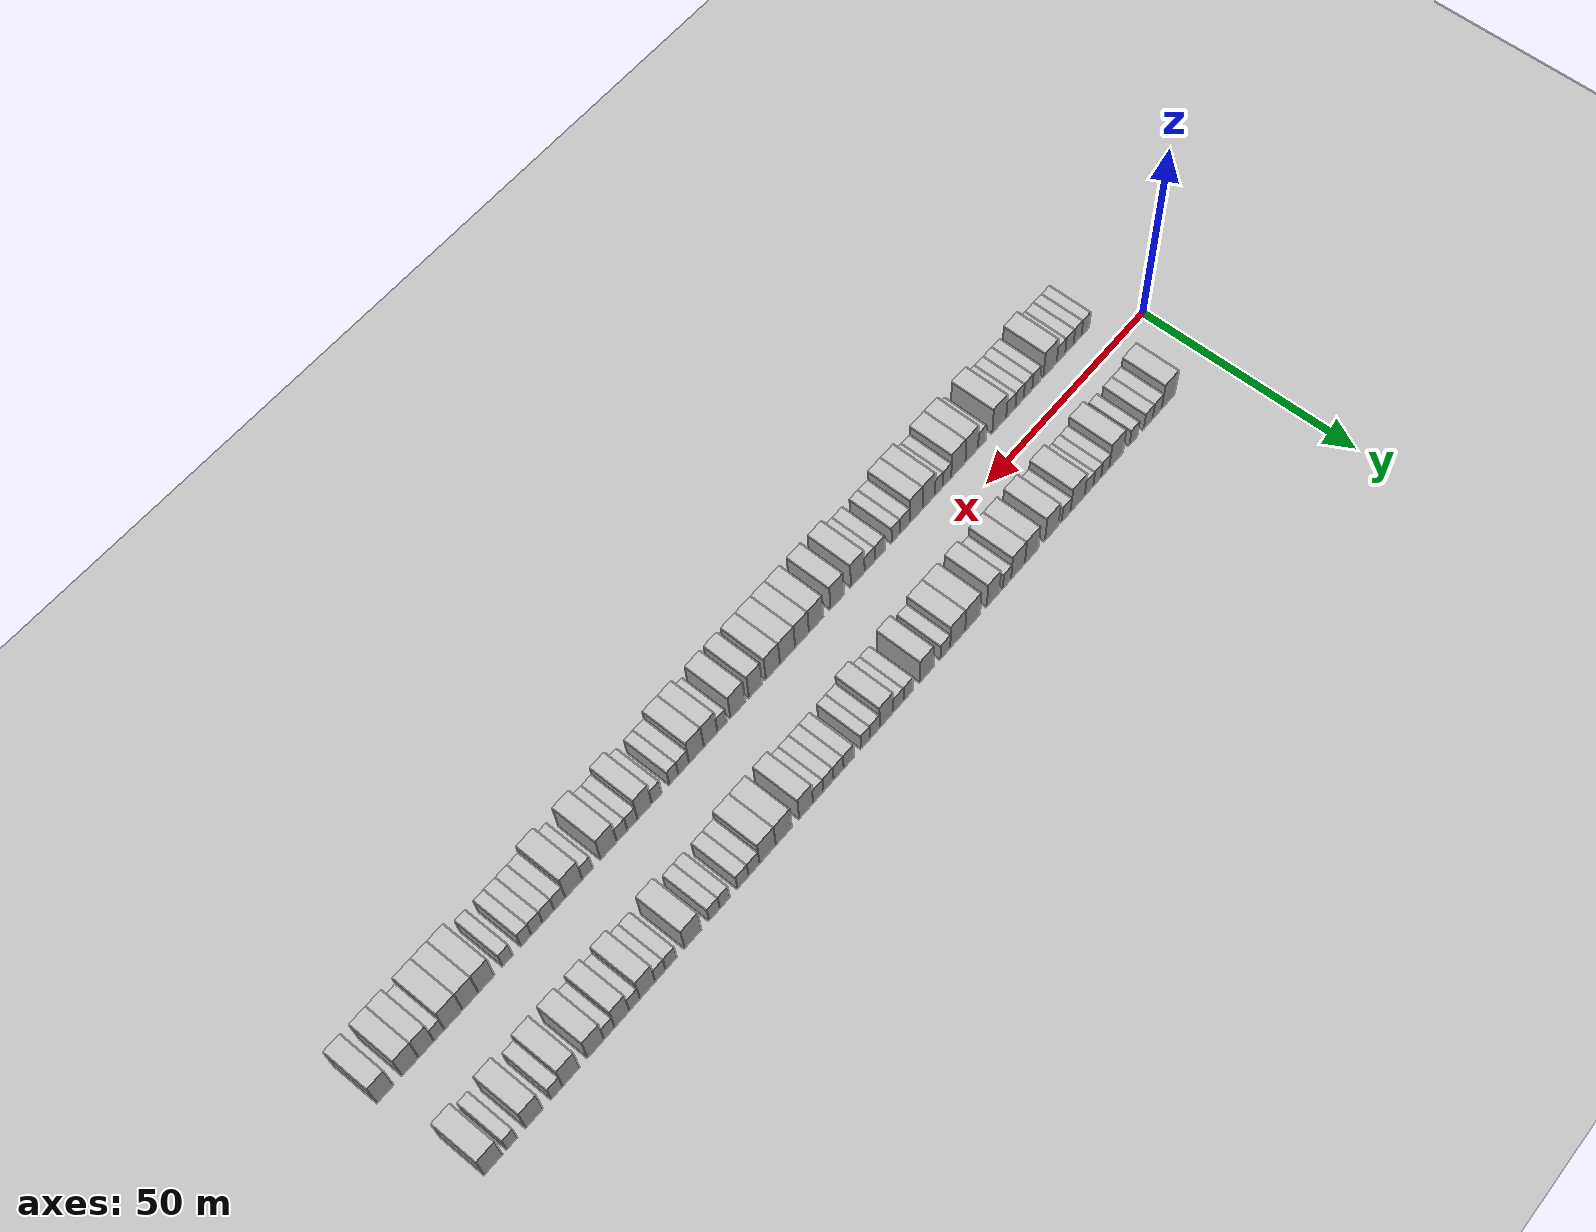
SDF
<?xml version="1.0" encoding="utf-8"?>

<sdf version="1.6">

   <world name="default">

      <gui fullscreen="0">

         <camera name="user_camera">

            <pose>-15 0 4.57585 0 0 0</pose>

            <view_controller>orbit</view_controller>

         </camera>

      </gui>

      <scene>

         <sky>

           <clouds>

             <speed>12</speed>

           </clouds>

         </sky>

         <ambient>0.4 0.4 0.4 1</ambient>

         <background>0.7 0.7 0.7 1</background>

         <shadows>1</shadows>

      </scene>

      <gravity>0 0 -9.8066</gravity>

      <magnetic_field>6e-06 2.3e-05 -4.2e-05</magnetic_field>

      <physics default="0" name="default_physics" type="ode">

         <ode>

            <solver>

               <type>quick</type>

               <iters>10</iters>

               <sor>1.0</sor>

               <use_dynamic_moi_rescaling>0</use_dynamic_moi_rescaling>

            </solver>

            <constraints>

               <cfm>0</cfm>

               <erp>0.2</erp>

               <contact_max_correcting_vel>100</contact_max_correcting_vel>

               <contact_surface_layer>0.001</contact_surface_layer>

            </constraints>

         </ode>

         <max_step_size>0.004</max_step_size>

         <real_time_factor>1</real_time_factor>

         <real_time_update_rate>250</real_time_update_rate>

      </physics>

      <light name="sun" type="directional">

         <cast_shadows>1</cast_shadows>

         <pose>0 0 10 0 0 0</pose>

         <diffuse>0.8 0.8 0.8 1</diffuse>

         <specular>0.2 0.2 0.2 1</specular>

         <attenuation>

            <range>1000</range>

            <constant>0.9</constant>

            <linear>0.01</linear>

            <quadratic>0.001</quadratic>

         </attenuation>

         <direction>-0.5 0.1 -0.9</direction>

      </light>

      <include>

         <name>ground_plane_1</name>

         <uri>model://HANNAS_ground_plane</uri>

         <pose>0 0 0  0 0 0</pose>

      </include>

      <include>

         <name>ground_plane_2</name>

         <uri>model://HANNAS_ground_plane</uri>

         <pose>100 0 0  0 0 0</pose>

      </include>

      <model name="building_1">

         <static>1</static>

         <pose frame="">14.1916 11.0000 0 0.000000 0.000000 1.570796</pose>

         <link name="link">

            <pose frame="">0 0 4.50 0 0 0</pose>

            <collision name="collision">

               <geometry>

                  <box>

                     <size>10.0000 4.3833 9.0000</size>

                  </box>

               </geometry>

               <max_contacts>10</max_contacts>

               <surface>

                  <contact>

                     <ode/>

                  </contact>

                  <bounce/>

                  <friction>

                     <torsional>

                        <ode/>

                     </torsional>

                     <ode/>

                  </friction>

               </surface>

            </collision>

            <visual name="visual">

               <cast_shadows>0</cast_shadows>

               <geometry>

                  <box>

                     <size>10.0000 4.3833 9.0000</size>

                  </box>

               </geometry>

               <material>

                  <script>

                     <uri>model://HANNAS_wall/materials/scripts</uri>

                     <uri>model://HANNAS_wall/materials/textures</uri>

                     <name>vrc/HANNAS_wall</name>

                  </script>

               </material>

            </visual>

            <self_collide>0</self_collide>

            <enable_wind>0</enable_wind>

            <kinematic>0</kinematic>

         </link>

      </model>

      <model name="building_2">

         <static>1</static>

         <pose frame="">17.8584 11.0000 0 0.000000 0.000000 1.570796</pose>

         <link name="link">

            <pose frame="">0 0 3.00 0 0 0</pose>

            <collision name="collision">

               <geometry>

                  <box>

                     <size>10.0000 2.9503 6.0000</size>

                  </box>

               </geometry>

               <max_contacts>10</max_contacts>

               <surface>

                  <contact>

                     <ode/>

                  </contact>

                  <bounce/>

                  <friction>

                     <torsional>

                        <ode/>

                     </torsional>

                     <ode/>

                  </friction>

               </surface>

            </collision>

            <visual name="visual">

               <cast_shadows>0</cast_shadows>

               <geometry>

                  <box>

                     <size>10.0000 2.9503 6.0000</size>

                  </box>

               </geometry>

               <material>

                  <script>

                     <uri>model://HANNAS_wall/materials/scripts</uri>

                     <uri>model://HANNAS_wall/materials/textures</uri>

                     <name>vrc/HANNAS_wall</name>

                  </script>

               </material>

            </visual>

            <self_collide>0</self_collide>

            <enable_wind>0</enable_wind>

            <kinematic>0</kinematic>

         </link>

      </model>

      <model name="building_3">

         <static>1</static>

         <pose frame="">20.7681 11.0000 0 0.000000 0.000000 1.570796</pose>

         <link name="link">

            <pose frame="">0 0 3.00 0 0 0</pose>

            <collision name="collision">

               <geometry>

                  <box>

                     <size>10.0000 2.8691 6.0000</size>

                  </box>

               </geometry>

               <max_contacts>10</max_contacts>

               <surface>

                  <contact>

                     <ode/>

                  </contact>

                  <bounce/>

                  <friction>

                     <torsional>

                        <ode/>

                     </torsional>

                     <ode/>

                  </friction>

               </surface>

            </collision>

            <visual name="visual">

               <cast_shadows>0</cast_shadows>

               <geometry>

                  <box>

                     <size>10.0000 2.8691 6.0000</size>

                  </box>

               </geometry>

               <material>

                  <script>

                     <uri>model://HANNAS_wall/materials/scripts</uri>

                     <uri>model://HANNAS_wall/materials/textures</uri>

                     <name>vrc/HANNAS_wall</name>

                  </script>

               </material>

            </visual>

            <self_collide>0</self_collide>

            <enable_wind>0</enable_wind>

            <kinematic>0</kinematic>

         </link>

      </model>

      <model name="building_4">

         <static>1</static>

         <pose frame="">25.5156 11.0000 0 0.000000 0.000000 1.570796</pose>

         <link name="link">

            <pose frame="">0 0 3.00 0 0 0</pose>

            <collision name="collision">

               <geometry>

                  <box>

                     <size>10.0000 2.6258 6.0000</size>

                  </box>

               </geometry>

               <max_contacts>10</max_contacts>

               <surface>

                  <contact>

                     <ode/>

                  </contact>

                  <bounce/>

                  <friction>

                     <torsional>

                        <ode/>

                     </torsional>

                     <ode/>

                  </friction>

               </surface>

            </collision>

            <visual name="visual">

               <cast_shadows>0</cast_shadows>

               <geometry>

                  <box>

                     <size>10.0000 2.6258 6.0000</size>

                  </box>

               </geometry>

               <material>

                  <script>

                     <uri>model://HANNAS_wall/materials/scripts</uri>

                     <uri>model://HANNAS_wall/materials/textures</uri>

                     <name>vrc/HANNAS_wall</name>

                  </script>

               </material>

            </visual>

            <self_collide>0</self_collide>

            <enable_wind>0</enable_wind>

            <kinematic>0</kinematic>

         </link>

      </model>

      <model name="building_5">

         <static>1</static>

         <pose frame="">31.0541 11.0000 0 0.000000 0.000000 1.570796</pose>

         <link name="link">

            <pose frame="">0 0 4.50 0 0 0</pose>

            <collision name="collision">

               <geometry>

                  <box>

                     <size>10.0000 4.4512 9.0000</size>

                  </box>

               </geometry>

               <max_contacts>10</max_contacts>

               <surface>

                  <contact>

                     <ode/>

                  </contact>

                  <bounce/>

                  <friction>

                     <torsional>

                        <ode/>

                     </torsional>

                     <ode/>

                  </friction>

               </surface>

            </collision>

            <visual name="visual">

               <cast_shadows>0</cast_shadows>

               <geometry>

                  <box>

                     <size>10.0000 4.4512 9.0000</size>

                  </box>

               </geometry>

               <material>

                  <script>

                     <uri>model://HANNAS_wall/materials/scripts</uri>

                     <uri>model://HANNAS_wall/materials/textures</uri>

                     <name>vrc/HANNAS_wall</name>

                  </script>

               </material>

            </visual>

            <self_collide>0</self_collide>

            <enable_wind>0</enable_wind>

            <kinematic>0</kinematic>

         </link>

      </model>

      <model name="building_6">

         <static>1</static>

         <pose frame="">34.5564 11.0000 0 0.000000 0.000000 1.570796</pose>

         <link name="link">

            <pose frame="">0 0 3.00 0 0 0</pose>

            <collision name="collision">

               <geometry>

                  <box>

                     <size>10.0000 2.5535 6.0000</size>

                  </box>

               </geometry>

               <max_contacts>10</max_contacts>

               <surface>

                  <contact>

                     <ode/>

                  </contact>

                  <bounce/>

                  <friction>

                     <torsional>

                        <ode/>

                     </torsional>

                     <ode/>

                  </friction>

               </surface>

            </collision>

            <visual name="visual">

               <cast_shadows>0</cast_shadows>

               <geometry>

                  <box>

                     <size>10.0000 2.5535 6.0000</size>

                  </box>

               </geometry>

               <material>

                  <script>

                     <uri>model://HANNAS_wall/materials/scripts</uri>

                     <uri>model://HANNAS_wall/materials/textures</uri>

                     <name>vrc/HANNAS_wall</name>

                  </script>

               </material>

            </visual>

            <self_collide>0</self_collide>

            <enable_wind>0</enable_wind>

            <kinematic>0</kinematic>

         </link>

      </model>

      <model name="building_7">

         <static>1</static>

         <pose frame="">37.0680 11.0000 0 0.000000 0.000000 1.570796</pose>

         <link name="link">

            <pose frame="">0 0 3.00 0 0 0</pose>

            <collision name="collision">

               <geometry>

                  <box>

                     <size>10.0000 2.4696 6.0000</size>

                  </box>

               </geometry>

               <max_contacts>10</max_contacts>

               <surface>

                  <contact>

                     <ode/>

                  </contact>

                  <bounce/>

                  <friction>

                     <torsional>

                        <ode/>

                     </torsional>

                     <ode/>

                  </friction>

               </surface>

            </collision>

            <visual name="visual">

               <cast_shadows>0</cast_shadows>

               <geometry>

                  <box>

                     <size>10.0000 2.4696 6.0000</size>

                  </box>

               </geometry>

               <material>

                  <script>

                     <uri>model://HANNAS_wall/materials/scripts</uri>

                     <uri>model://HANNAS_wall/materials/textures</uri>

                     <name>vrc/HANNAS_wall</name>

                  </script>

               </material>

            </visual>

            <self_collide>0</self_collide>

            <enable_wind>0</enable_wind>

            <kinematic>0</kinematic>

         </link>

      </model>

      <model name="building_8">

         <static>1</static>

         <pose frame="">39.6554 11.0000 0 0.000000 0.000000 1.570796</pose>

         <link name="link">

            <pose frame="">0 0 3.00 0 0 0</pose>

            <collision name="collision">

               <geometry>

                  <box>

                     <size>10.0000 2.7051 6.0000</size>

                  </box>

               </geometry>

               <max_contacts>10</max_contacts>

               <surface>

                  <contact>

                     <ode/>

                  </contact>

                  <bounce/>

                  <friction>

                     <torsional>

                        <ode/>

                     </torsional>

                     <ode/>

                  </friction>

               </surface>

            </collision>

            <visual name="visual">

               <cast_shadows>0</cast_shadows>

               <geometry>

                  <box>

                     <size>10.0000 2.7051 6.0000</size>

                  </box>

               </geometry>

               <material>

                  <script>

                     <uri>model://HANNAS_wall/materials/scripts</uri>

                     <uri>model://HANNAS_wall/materials/textures</uri>

                     <name>vrc/HANNAS_wall</name>

                  </script>

               </material>

            </visual>

            <self_collide>0</self_collide>

            <enable_wind>0</enable_wind>

            <kinematic>0</kinematic>

         </link>

      </model>

      <model name="building_9">

         <static>1</static>

         <pose frame="">43.2333 11.0000 0 0.000000 0.000000 1.570796</pose>

         <link name="link">

            <pose frame="">0 0 4.50 0 0 0</pose>

            <collision name="collision">

               <geometry>

                  <box>

                     <size>10.0000 4.4507 9.0000</size>

                  </box>

               </geometry>

               <max_contacts>10</max_contacts>

               <surface>

                  <contact>

                     <ode/>

                  </contact>

                  <bounce/>

                  <friction>

                     <torsional>

                        <ode/>

                     </torsional>

                     <ode/>

                  </friction>

               </surface>

            </collision>

            <visual name="visual">

               <cast_shadows>0</cast_shadows>

               <geometry>

                  <box>

                     <size>10.0000 4.4507 9.0000</size>

                  </box>

               </geometry>

               <material>

                  <script>

                     <uri>model://HANNAS_wall/materials/scripts</uri>

                     <uri>model://HANNAS_wall/materials/textures</uri>

                     <name>vrc/HANNAS_wall</name>

                  </script>

               </material>

            </visual>

            <self_collide>0</self_collide>

            <enable_wind>0</enable_wind>

            <kinematic>0</kinematic>

         </link>

      </model>

      <model name="building_10">

         <static>1</static>

         <pose frame="">46.8315 11.0000 0 0.000000 0.000000 1.570796</pose>

         <link name="link">

            <pose frame="">0 0 3.00 0 0 0</pose>

            <collision name="collision">

               <geometry>

                  <box>

                     <size>10.0000 2.7459 6.0000</size>

                  </box>

               </geometry>

               <max_contacts>10</max_contacts>

               <surface>

                  <contact>

                     <ode/>

                  </contact>

                  <bounce/>

                  <friction>

                     <torsional>

                        <ode/>

                     </torsional>

                     <ode/>

                  </friction>

               </surface>

            </collision>

            <visual name="visual">

               <cast_shadows>0</cast_shadows>

               <geometry>

                  <box>

                     <size>10.0000 2.7459 6.0000</size>

                  </box>

               </geometry>

               <material>

                  <script>

                     <uri>model://HANNAS_wall/materials/scripts</uri>

                     <uri>model://HANNAS_wall/materials/textures</uri>

                     <name>vrc/HANNAS_wall</name>

                  </script>

               </material>

            </visual>

            <self_collide>0</self_collide>

            <enable_wind>0</enable_wind>

            <kinematic>0</kinematic>

         </link>

      </model>

      <model name="building_11">

         <static>1</static>

         <pose frame="">51.2808 11.0000 0 0.000000 0.000000 1.570796</pose>

         <link name="link">

            <pose frame="">0 0 4.50 0 0 0</pose>

            <collision name="collision">

               <geometry>

                  <box>

                     <size>10.0000 4.1526 9.0000</size>

                  </box>

               </geometry>

               <max_contacts>10</max_contacts>

               <surface>

                  <contact>

                     <ode/>

                  </contact>

                  <bounce/>

                  <friction>

                     <torsional>

                        <ode/>

                     </torsional>

                     <ode/>

                  </friction>

               </surface>

            </collision>

            <visual name="visual">

               <cast_shadows>0</cast_shadows>

               <geometry>

                  <box>

                     <size>10.0000 4.1526 9.0000</size>

                  </box>

               </geometry>

               <material>

                  <script>

                     <uri>model://HANNAS_wall/materials/scripts</uri>

                     <uri>model://HANNAS_wall/materials/textures</uri>

                     <name>vrc/HANNAS_wall</name>

                  </script>

               </material>

            </visual>

            <self_collide>0</self_collide>

            <enable_wind>0</enable_wind>

            <kinematic>0</kinematic>

         </link>

      </model>

      <model name="building_12">

         <static>1</static>

         <pose frame="">57.4109 11.0000 0 0.000000 0.000000 1.570796</pose>

         <link name="link">

            <pose frame="">0 0 4.50 0 0 0</pose>

            <collision name="collision">

               <geometry>

                  <box>

                     <size>10.0000 4.1077 9.0000</size>

                  </box>

               </geometry>

               <max_contacts>10</max_contacts>

               <surface>

                  <contact>

                     <ode/>

                  </contact>

                  <bounce/>

                  <friction>

                     <torsional>

                        <ode/>

                     </torsional>

                     <ode/>

                  </friction>

               </surface>

            </collision>

            <visual name="visual">

               <cast_shadows>0</cast_shadows>

               <geometry>

                  <box>

                     <size>10.0000 4.1077 9.0000</size>

                  </box>

               </geometry>

               <material>

                  <script>

                     <uri>model://HANNAS_wall/materials/scripts</uri>

                     <uri>model://HANNAS_wall/materials/textures</uri>

                     <name>vrc/HANNAS_wall</name>

                  </script>

               </material>

            </visual>

            <self_collide>0</self_collide>

            <enable_wind>0</enable_wind>

            <kinematic>0</kinematic>

         </link>

      </model>

      <model name="building_13">

         <static>1</static>

         <pose frame="">61.5724 11.0000 0 0.000000 0.000000 1.570796</pose>

         <link name="link">

            <pose frame="">0 0 4.50 0 0 0</pose>

            <collision name="collision">

               <geometry>

                  <box>

                     <size>10.0000 4.2152 9.0000</size>

                  </box>

               </geometry>

               <max_contacts>10</max_contacts>

               <surface>

                  <contact>

                     <ode/>

                  </contact>

                  <bounce/>

                  <friction>

                     <torsional>

                        <ode/>

                     </torsional>

                     <ode/>

                  </friction>

               </surface>

            </collision>

            <visual name="visual">

               <cast_shadows>0</cast_shadows>

               <geometry>

                  <box>

                     <size>10.0000 4.2152 9.0000</size>

                  </box>

               </geometry>

               <material>

                  <script>

                     <uri>model://HANNAS_wall/materials/scripts</uri>

                     <uri>model://HANNAS_wall/materials/textures</uri>

                     <name>vrc/HANNAS_wall</name>

                  </script>

               </material>

            </visual>

            <self_collide>0</self_collide>

            <enable_wind>0</enable_wind>

            <kinematic>0</kinematic>

         </link>

      </model>

      <model name="building_14">

         <static>1</static>

         <pose frame="">64.9226 11.0000 0 0.000000 0.000000 1.570796</pose>

         <link name="link">

            <pose frame="">0 0 3.00 0 0 0</pose>

            <collision name="collision">

               <geometry>

                  <box>

                     <size>10.0000 2.4853 6.0000</size>

                  </box>

               </geometry>

               <max_contacts>10</max_contacts>

               <surface>

                  <contact>

                     <ode/>

                  </contact>

                  <bounce/>

                  <friction>

                     <torsional>

                        <ode/>

                     </torsional>

                     <ode/>

                  </friction>

               </surface>

            </collision>

            <visual name="visual">

               <cast_shadows>0</cast_shadows>

               <geometry>

                  <box>

                     <size>10.0000 2.4853 6.0000</size>

                  </box>

               </geometry>

               <material>

                  <script>

                     <uri>model://HANNAS_wall/materials/scripts</uri>

                     <uri>model://HANNAS_wall/materials/textures</uri>

                     <name>vrc/HANNAS_wall</name>

                  </script>

               </material>

            </visual>

            <self_collide>0</self_collide>

            <enable_wind>0</enable_wind>

            <kinematic>0</kinematic>

         </link>

      </model>

      <model name="building_15">

         <static>1</static>

         <pose frame="">69.0574 11.0000 0 0.000000 0.000000 1.570796</pose>

         <link name="link">

            <pose frame="">0 0 4.50 0 0 0</pose>

            <collision name="collision">

               <geometry>

                  <box>

                     <size>10.0000 3.7844 9.0000</size>

                  </box>

               </geometry>

               <max_contacts>10</max_contacts>

               <surface>

                  <contact>

                     <ode/>

                  </contact>

                  <bounce/>

                  <friction>

                     <torsional>

                        <ode/>

                     </torsional>

                     <ode/>

                  </friction>

               </surface>

            </collision>

            <visual name="visual">

               <cast_shadows>0</cast_shadows>

               <geometry>

                  <box>

                     <size>10.0000 3.7844 9.0000</size>

                  </box>

               </geometry>

               <material>

                  <script>

                     <uri>model://HANNAS_wall/materials/scripts</uri>

                     <uri>model://HANNAS_wall/materials/textures</uri>

                     <name>vrc/HANNAS_wall</name>

                  </script>

               </material>

            </visual>

            <self_collide>0</self_collide>

            <enable_wind>0</enable_wind>

            <kinematic>0</kinematic>

         </link>

      </model>

      <model name="building_16">

         <static>1</static>

         <pose frame="">75.1733 11.0000 0 0.000000 0.000000 1.570796</pose>

         <link name="link">

            <pose frame="">0 0 4.50 0 0 0</pose>

            <collision name="collision">

               <geometry>

                  <box>

                     <size>10.0000 4.4473 9.0000</size>

                  </box>

               </geometry>

               <max_contacts>10</max_contacts>

               <surface>

                  <contact>

                     <ode/>

                  </contact>

                  <bounce/>

                  <friction>

                     <torsional>

                        <ode/>

                     </torsional>

                     <ode/>

                  </friction>

               </surface>

            </collision>

            <visual name="visual">

               <cast_shadows>0</cast_shadows>

               <geometry>

                  <box>

                     <size>10.0000 4.4473 9.0000</size>

                  </box>

               </geometry>

               <material>

                  <script>

                     <uri>model://HANNAS_wall/materials/scripts</uri>

                     <uri>model://HANNAS_wall/materials/textures</uri>

                     <name>vrc/HANNAS_wall</name>

                  </script>

               </material>

            </visual>

            <self_collide>0</self_collide>

            <enable_wind>0</enable_wind>

            <kinematic>0</kinematic>

         </link>

      </model>

      <model name="building_17">

         <static>1</static>

         <pose frame="">79.6025 11.0000 0 0.000000 0.000000 1.570796</pose>

         <link name="link">

            <pose frame="">0 0 4.50 0 0 0</pose>

            <collision name="collision">

               <geometry>

                  <box>

                     <size>10.0000 4.4111 9.0000</size>

                  </box>

               </geometry>

               <max_contacts>10</max_contacts>

               <surface>

                  <contact>

                     <ode/>

                  </contact>

                  <bounce/>

                  <friction>

                     <torsional>

                        <ode/>

                     </torsional>

                     <ode/>

                  </friction>

               </surface>

            </collision>

            <visual name="visual">

               <cast_shadows>0</cast_shadows>

               <geometry>

                  <box>

                     <size>10.0000 4.4111 9.0000</size>

                  </box>

               </geometry>

               <material>

                  <script>

                     <uri>model://HANNAS_wall/materials/scripts</uri>

                     <uri>model://HANNAS_wall/materials/textures</uri>

                     <name>vrc/HANNAS_wall</name>

                  </script>

               </material>

            </visual>

            <self_collide>0</self_collide>

            <enable_wind>0</enable_wind>

            <kinematic>0</kinematic>

         </link>

      </model>

      <model name="building_18">

         <static>1</static>

         <pose frame="">83.2336 11.0000 0 0.000000 0.000000 1.570796</pose>

         <link name="link">

            <pose frame="">0 0 3.00 0 0 0</pose>

            <collision name="collision">

               <geometry>

                  <box>

                     <size>10.0000 2.8511 6.0000</size>

                  </box>

               </geometry>

               <max_contacts>10</max_contacts>

               <surface>

                  <contact>

                     <ode/>

                  </contact>

                  <bounce/>

                  <friction>

                     <torsional>

                        <ode/>

                     </torsional>

                     <ode/>

                  </friction>

               </surface>

            </collision>

            <visual name="visual">

               <cast_shadows>0</cast_shadows>

               <geometry>

                  <box>

                     <size>10.0000 2.8511 6.0000</size>

                  </box>

               </geometry>

               <material>

                  <script>

                     <uri>model://HANNAS_wall/materials/scripts</uri>

                     <uri>model://HANNAS_wall/materials/textures</uri>

                     <name>vrc/HANNAS_wall</name>

                  </script>

               </material>

            </visual>

            <self_collide>0</self_collide>

            <enable_wind>0</enable_wind>

            <kinematic>0</kinematic>

         </link>

      </model>

      <model name="building_19">

         <static>1</static>

         <pose frame="">88.6047 11.0000 0 0.000000 0.000000 1.570796</pose>

         <link name="link">

            <pose frame="">0 0 4.50 0 0 0</pose>

            <collision name="collision">

               <geometry>

                  <box>

                     <size>10.0000 3.8911 9.0000</size>

                  </box>

               </geometry>

               <max_contacts>10</max_contacts>

               <surface>

                  <contact>

                     <ode/>

                  </contact>

                  <bounce/>

                  <friction>

                     <torsional>

                        <ode/>

                     </torsional>

                     <ode/>

                  </friction>

               </surface>

            </collision>

            <visual name="visual">

               <cast_shadows>0</cast_shadows>

               <geometry>

                  <box>

                     <size>10.0000 3.8911 9.0000</size>

                  </box>

               </geometry>

               <material>

                  <script>

                     <uri>model://HANNAS_wall/materials/scripts</uri>

                     <uri>model://HANNAS_wall/materials/textures</uri>

                     <name>vrc/HANNAS_wall</name>

                  </script>

               </material>

            </visual>

            <self_collide>0</self_collide>

            <enable_wind>0</enable_wind>

            <kinematic>0</kinematic>

         </link>

      </model>

      <model name="building_20">

         <static>1</static>

         <pose frame="">93.9447 11.0000 0 0.000000 0.000000 1.570796</pose>

         <link name="link">

            <pose frame="">0 0 3.00 0 0 0</pose>

            <collision name="collision">

               <geometry>

                  <box>

                     <size>10.0000 2.7890 6.0000</size>

                  </box>

               </geometry>

               <max_contacts>10</max_contacts>

               <surface>

                  <contact>

                     <ode/>

                  </contact>

                  <bounce/>

                  <friction>

                     <torsional>

                        <ode/>

                     </torsional>

                     <ode/>

                  </friction>

               </surface>

            </collision>

            <visual name="visual">

               <cast_shadows>0</cast_shadows>

               <geometry>

                  <box>

                     <size>10.0000 2.7890 6.0000</size>

                  </box>

               </geometry>

               <material>

                  <script>

                     <uri>model://HANNAS_wall/materials/scripts</uri>

                     <uri>model://HANNAS_wall/materials/textures</uri>

                     <name>vrc/HANNAS_wall</name>

                  </script>

               </material>

            </visual>

            <self_collide>0</self_collide>

            <enable_wind>0</enable_wind>

            <kinematic>0</kinematic>

         </link>

      </model>

      <model name="building_21">

         <static>1</static>

         <pose frame="">96.7968 11.0000 0 0.000000 0.000000 1.570796</pose>

         <link name="link">

            <pose frame="">0 0 3.00 0 0 0</pose>

            <collision name="collision">

               <geometry>

                  <box>

                     <size>10.0000 2.9152 6.0000</size>

                  </box>

               </geometry>

               <max_contacts>10</max_contacts>

               <surface>

                  <contact>

                     <ode/>

                  </contact>

                  <bounce/>

                  <friction>

                     <torsional>

                        <ode/>

                     </torsional>

                     <ode/>

                  </friction>

               </surface>

            </collision>

            <visual name="visual">

               <cast_shadows>0</cast_shadows>

               <geometry>

                  <box>

                     <size>10.0000 2.9152 6.0000</size>

                  </box>

               </geometry>

               <material>

                  <script>

                     <uri>model://HANNAS_wall/materials/scripts</uri>

                     <uri>model://HANNAS_wall/materials/textures</uri>

                     <name>vrc/HANNAS_wall</name>

                  </script>

               </material>

            </visual>

            <self_collide>0</self_collide>

            <enable_wind>0</enable_wind>

            <kinematic>0</kinematic>

         </link>

      </model>

      <model name="building_22">

         <static>1</static>

         <pose frame="">100.1815 11.0000 0 0.000000 0.000000 1.570796</pose>

         <link name="link">

            <pose frame="">0 0 4.50 0 0 0</pose>

            <collision name="collision">

               <geometry>

                  <box>

                     <size>10.0000 3.8543 9.0000</size>

                  </box>

               </geometry>

               <max_contacts>10</max_contacts>

               <surface>

                  <contact>

                     <ode/>

                  </contact>

                  <bounce/>

                  <friction>

                     <torsional>

                        <ode/>

                     </torsional>

                     <ode/>

                  </friction>

               </surface>

            </collision>

            <visual name="visual">

               <cast_shadows>0</cast_shadows>

               <geometry>

                  <box>

                     <size>10.0000 3.8543 9.0000</size>

                  </box>

               </geometry>

               <material>

                  <script>

                     <uri>model://HANNAS_wall/materials/scripts</uri>

                     <uri>model://HANNAS_wall/materials/textures</uri>

                     <name>vrc/HANNAS_wall</name>

                  </script>

               </material>

            </visual>

            <self_collide>0</self_collide>

            <enable_wind>0</enable_wind>

            <kinematic>0</kinematic>

         </link>

      </model>

      <model name="building_23">

         <static>1</static>

         <pose frame="">103.4784 11.0000 0 0.000000 0.000000 1.570796</pose>

         <link name="link">

            <pose frame="">0 0 3.00 0 0 0</pose>

            <collision name="collision">

               <geometry>

                  <box>

                     <size>10.0000 2.7394 6.0000</size>

                  </box>

               </geometry>

               <max_contacts>10</max_contacts>

               <surface>

                  <contact>

                     <ode/>

                  </contact>

                  <bounce/>

                  <friction>

                     <torsional>

                        <ode/>

                     </torsional>

                     <ode/>

                  </friction>

               </surface>

            </collision>

            <visual name="visual">

               <cast_shadows>0</cast_shadows>

               <geometry>

                  <box>

                     <size>10.0000 2.7394 6.0000</size>

                  </box>

               </geometry>

               <material>

                  <script>

                     <uri>model://HANNAS_wall/materials/scripts</uri>

                     <uri>model://HANNAS_wall/materials/textures</uri>

                     <name>vrc/HANNAS_wall</name>

                  </script>

               </material>

            </visual>

            <self_collide>0</self_collide>

            <enable_wind>0</enable_wind>

            <kinematic>0</kinematic>

         </link>

      </model>

      <model name="building_24">

         <static>1</static>

         <pose frame="">106.0939 11.0000 0 0.000000 0.000000 1.570796</pose>

         <link name="link">

            <pose frame="">0 0 3.00 0 0 0</pose>

            <collision name="collision">

               <geometry>

                  <box>

                     <size>10.0000 2.4915 6.0000</size>

                  </box>

               </geometry>

               <max_contacts>10</max_contacts>

               <surface>

                  <contact>

                     <ode/>

                  </contact>

                  <bounce/>

                  <friction>

                     <torsional>

                        <ode/>

                     </torsional>

                     <ode/>

                  </friction>

               </surface>

            </collision>

            <visual name="visual">

               <cast_shadows>0</cast_shadows>

               <geometry>

                  <box>

                     <size>10.0000 2.4915 6.0000</size>

                  </box>

               </geometry>

               <material>

                  <script>

                     <uri>model://HANNAS_wall/materials/scripts</uri>

                     <uri>model://HANNAS_wall/materials/textures</uri>

                     <name>vrc/HANNAS_wall</name>

                  </script>

               </material>

            </visual>

            <self_collide>0</self_collide>

            <enable_wind>0</enable_wind>

            <kinematic>0</kinematic>

         </link>

      </model>

      <model name="building_25">

         <static>1</static>

         <pose frame="">110.7902 11.0000 0 0.000000 0.000000 1.570796</pose>

         <link name="link">

            <pose frame="">0 0 3.00 0 0 0</pose>

            <collision name="collision">

               <geometry>

                  <box>

                     <size>10.0000 2.9011 6.0000</size>

                  </box>

               </geometry>

               <max_contacts>10</max_contacts>

               <surface>

                  <contact>

                     <ode/>

                  </contact>

                  <bounce/>

                  <friction>

                     <torsional>

                        <ode/>

                     </torsional>

                     <ode/>

                  </friction>

               </surface>

            </collision>

            <visual name="visual">

               <cast_shadows>0</cast_shadows>

               <geometry>

                  <box>

                     <size>10.0000 2.9011 6.0000</size>

                  </box>

               </geometry>

               <material>

                  <script>

                     <uri>model://HANNAS_wall/materials/scripts</uri>

                     <uri>model://HANNAS_wall/materials/textures</uri>

                     <name>vrc/HANNAS_wall</name>

                  </script>

               </material>

            </visual>

            <self_collide>0</self_collide>

            <enable_wind>0</enable_wind>

            <kinematic>0</kinematic>

         </link>

      </model>

      <model name="building_26">

         <static>1</static>

         <pose frame="">113.6350 11.0000 0 0.000000 0.000000 1.570796</pose>

         <link name="link">

            <pose frame="">0 0 3.00 0 0 0</pose>

            <collision name="collision">

               <geometry>

                  <box>

                     <size>10.0000 2.7884 6.0000</size>

                  </box>

               </geometry>

               <max_contacts>10</max_contacts>

               <surface>

                  <contact>

                     <ode/>

                  </contact>

                  <bounce/>

                  <friction>

                     <torsional>

                        <ode/>

                     </torsional>

                     <ode/>

                  </friction>

               </surface>

            </collision>

            <visual name="visual">

               <cast_shadows>0</cast_shadows>

               <geometry>

                  <box>

                     <size>10.0000 2.7884 6.0000</size>

                  </box>

               </geometry>

               <material>

                  <script>

                     <uri>model://HANNAS_wall/materials/scripts</uri>

                     <uri>model://HANNAS_wall/materials/textures</uri>

                     <name>vrc/HANNAS_wall</name>

                  </script>

               </material>

            </visual>

            <self_collide>0</self_collide>

            <enable_wind>0</enable_wind>

            <kinematic>0</kinematic>

         </link>

      </model>

      <model name="building_27">

         <static>1</static>

         <pose frame="">116.4411 11.0000 0 0.000000 0.000000 1.570796</pose>

         <link name="link">

            <pose frame="">0 0 3.00 0 0 0</pose>

            <collision name="collision">

               <geometry>

                  <box>

                     <size>10.0000 2.8239 6.0000</size>

                  </box>

               </geometry>

               <max_contacts>10</max_contacts>

               <surface>

                  <contact>

                     <ode/>

                  </contact>

                  <bounce/>

                  <friction>

                     <torsional>

                        <ode/>

                     </torsional>

                     <ode/>

                  </friction>

               </surface>

            </collision>

            <visual name="visual">

               <cast_shadows>0</cast_shadows>

               <geometry>

                  <box>

                     <size>10.0000 2.8239 6.0000</size>

                  </box>

               </geometry>

               <material>

                  <script>

                     <uri>model://HANNAS_wall/materials/scripts</uri>

                     <uri>model://HANNAS_wall/materials/textures</uri>

                     <name>vrc/HANNAS_wall</name>

                  </script>

               </material>

            </visual>

            <self_collide>0</self_collide>

            <enable_wind>0</enable_wind>

            <kinematic>0</kinematic>

         </link>

      </model>

      <model name="building_28">

         <static>1</static>

         <pose frame="">119.2753 11.0000 0 0.000000 0.000000 1.570796</pose>

         <link name="link">

            <pose frame="">0 0 3.00 0 0 0</pose>

            <collision name="collision">

               <geometry>

                  <box>

                     <size>10.0000 2.8445 6.0000</size>

                  </box>

               </geometry>

               <max_contacts>10</max_contacts>

               <surface>

                  <contact>

                     <ode/>

                  </contact>

                  <bounce/>

                  <friction>

                     <torsional>

                        <ode/>

                     </torsional>

                     <ode/>

                  </friction>

               </surface>

            </collision>

            <visual name="visual">

               <cast_shadows>0</cast_shadows>

               <geometry>

                  <box>

                     <size>10.0000 2.8445 6.0000</size>

                  </box>

               </geometry>

               <material>

                  <script>

                     <uri>model://HANNAS_wall/materials/scripts</uri>

                     <uri>model://HANNAS_wall/materials/textures</uri>

                     <name>vrc/HANNAS_wall</name>

                  </script>

               </material>

            </visual>

            <self_collide>0</self_collide>

            <enable_wind>0</enable_wind>

            <kinematic>0</kinematic>

         </link>

      </model>

      <model name="building_29">

         <static>1</static>

         <pose frame="">122.5938 11.0000 0 0.000000 0.000000 1.570796</pose>

         <link name="link">

            <pose frame="">0 0 4.50 0 0 0</pose>

            <collision name="collision">

               <geometry>

                  <box>

                     <size>10.0000 3.7925 9.0000</size>

                  </box>

               </geometry>

               <max_contacts>10</max_contacts>

               <surface>

                  <contact>

                     <ode/>

                  </contact>

                  <bounce/>

                  <friction>

                     <torsional>

                        <ode/>

                     </torsional>

                     <ode/>

                  </friction>

               </surface>

            </collision>

            <visual name="visual">

               <cast_shadows>0</cast_shadows>

               <geometry>

                  <box>

                     <size>10.0000 3.7925 9.0000</size>

                  </box>

               </geometry>

               <material>

                  <script>

                     <uri>model://HANNAS_wall/materials/scripts</uri>

                     <uri>model://HANNAS_wall/materials/textures</uri>

                     <name>vrc/HANNAS_wall</name>

                  </script>

               </material>

            </visual>

            <self_collide>0</self_collide>

            <enable_wind>0</enable_wind>

            <kinematic>0</kinematic>

         </link>

      </model>

      <model name="building_30">

         <static>1</static>

         <pose frame="">128.6540 11.0000 0 0.000000 0.000000 1.570796</pose>

         <link name="link">

            <pose frame="">0 0 4.50 0 0 0</pose>

            <collision name="collision">

               <geometry>

                  <box>

                     <size>10.0000 4.3278 9.0000</size>

                  </box>

               </geometry>

               <max_contacts>10</max_contacts>

               <surface>

                  <contact>

                     <ode/>

                  </contact>

                  <bounce/>

                  <friction>

                     <torsional>

                        <ode/>

                     </torsional>

                     <ode/>

                  </friction>

               </surface>

            </collision>

            <visual name="visual">

               <cast_shadows>0</cast_shadows>

               <geometry>

                  <box>

                     <size>10.0000 4.3278 9.0000</size>

                  </box>

               </geometry>

               <material>

                  <script>

                     <uri>model://HANNAS_wall/materials/scripts</uri>

                     <uri>model://HANNAS_wall/materials/textures</uri>

                     <name>vrc/HANNAS_wall</name>

                  </script>

               </material>

            </visual>

            <self_collide>0</self_collide>

            <enable_wind>0</enable_wind>

            <kinematic>0</kinematic>

         </link>

      </model>

      <model name="building_31">

         <static>1</static>

         <pose frame="">132.9918 11.0000 0 0.000000 0.000000 1.570796</pose>

         <link name="link">

            <pose frame="">0 0 4.50 0 0 0</pose>

            <collision name="collision">

               <geometry>

                  <box>

                     <size>10.0000 4.3479 9.0000</size>

                  </box>

               </geometry>

               <max_contacts>10</max_contacts>

               <surface>

                  <contact>

                     <ode/>

                  </contact>

                  <bounce/>

                  <friction>

                     <torsional>

                        <ode/>

                     </torsional>

                     <ode/>

                  </friction>

               </surface>

            </collision>

            <visual name="visual">

               <cast_shadows>0</cast_shadows>

               <geometry>

                  <box>

                     <size>10.0000 4.3479 9.0000</size>

                  </box>

               </geometry>

               <material>

                  <script>

                     <uri>model://HANNAS_wall/materials/scripts</uri>

                     <uri>model://HANNAS_wall/materials/textures</uri>

                     <name>vrc/HANNAS_wall</name>

                  </script>

               </material>

            </visual>

            <self_collide>0</self_collide>

            <enable_wind>0</enable_wind>

            <kinematic>0</kinematic>

         </link>

      </model>

      <model name="building_32">

         <static>1</static>

         <pose frame="">136.6308 11.0000 0 0.000000 0.000000 1.570796</pose>

         <link name="link">

            <pose frame="">0 0 3.00 0 0 0</pose>

            <collision name="collision">

               <geometry>

                  <box>

                     <size>10.0000 2.9301 6.0000</size>

                  </box>

               </geometry>

               <max_contacts>10</max_contacts>

               <surface>

                  <contact>

                     <ode/>

                  </contact>

                  <bounce/>

                  <friction>

                     <torsional>

                        <ode/>

                     </torsional>

                     <ode/>

                  </friction>

               </surface>

            </collision>

            <visual name="visual">

               <cast_shadows>0</cast_shadows>

               <geometry>

                  <box>

                     <size>10.0000 2.9301 6.0000</size>

                  </box>

               </geometry>

               <material>

                  <script>

                     <uri>model://HANNAS_wall/materials/scripts</uri>

                     <uri>model://HANNAS_wall/materials/textures</uri>

                     <name>vrc/HANNAS_wall</name>

                  </script>

               </material>

            </visual>

            <self_collide>0</self_collide>

            <enable_wind>0</enable_wind>

            <kinematic>0</kinematic>

         </link>

      </model>

      <model name="building_33">

         <static>1</static>

         <pose frame="">139.5832 11.0000 0 0.000000 0.000000 1.570796</pose>

         <link name="link">

            <pose frame="">0 0 3.00 0 0 0</pose>

            <collision name="collision">

               <geometry>

                  <box>

                     <size>10.0000 2.9747 6.0000</size>

                  </box>

               </geometry>

               <max_contacts>10</max_contacts>

               <surface>

                  <contact>

                     <ode/>

                  </contact>

                  <bounce/>

                  <friction>

                     <torsional>

                        <ode/>

                     </torsional>

                     <ode/>

                  </friction>

               </surface>

            </collision>

            <visual name="visual">

               <cast_shadows>0</cast_shadows>

               <geometry>

                  <box>

                     <size>10.0000 2.9747 6.0000</size>

                  </box>

               </geometry>

               <material>

                  <script>

                     <uri>model://HANNAS_wall/materials/scripts</uri>

                     <uri>model://HANNAS_wall/materials/textures</uri>

                     <name>vrc/HANNAS_wall</name>

                  </script>

               </material>

            </visual>

            <self_collide>0</self_collide>

            <enable_wind>0</enable_wind>

            <kinematic>0</kinematic>

         </link>

      </model>

      <model name="building_34">

         <static>1</static>

         <pose frame="">144.3902 11.0000 0 0.000000 0.000000 1.570796</pose>

         <link name="link">

            <pose frame="">0 0 3.00 0 0 0</pose>

            <collision name="collision">

               <geometry>

                  <box>

                     <size>10.0000 2.6395 6.0000</size>

                  </box>

               </geometry>

               <max_contacts>10</max_contacts>

               <surface>

                  <contact>

                     <ode/>

                  </contact>

                  <bounce/>

                  <friction>

                     <torsional>

                        <ode/>

                     </torsional>

                     <ode/>

                  </friction>

               </surface>

            </collision>

            <visual name="visual">

               <cast_shadows>0</cast_shadows>

               <geometry>

                  <box>

                     <size>10.0000 2.6395 6.0000</size>

                  </box>

               </geometry>

               <material>

                  <script>

                     <uri>model://HANNAS_wall/materials/scripts</uri>

                     <uri>model://HANNAS_wall/materials/textures</uri>

                     <name>vrc/HANNAS_wall</name>

                  </script>

               </material>

            </visual>

            <self_collide>0</self_collide>

            <enable_wind>0</enable_wind>

            <kinematic>0</kinematic>

         </link>

      </model>

      <model name="building_35">

         <static>1</static>

         <pose frame="">147.1304 11.0000 0 0.000000 0.000000 1.570796</pose>

         <link name="link">

            <pose frame="">0 0 3.00 0 0 0</pose>

            <collision name="collision">

               <geometry>

                  <box>

                     <size>10.0000 2.8409 6.0000</size>

                  </box>

               </geometry>

               <max_contacts>10</max_contacts>

               <surface>

                  <contact>

                     <ode/>

                  </contact>

                  <bounce/>

                  <friction>

                     <torsional>

                        <ode/>

                     </torsional>

                     <ode/>

                  </friction>

               </surface>

            </collision>

            <visual name="visual">

               <cast_shadows>0</cast_shadows>

               <geometry>

                  <box>

                     <size>10.0000 2.8409 6.0000</size>

                  </box>

               </geometry>

               <material>

                  <script>

                     <uri>model://HANNAS_wall/materials/scripts</uri>

                     <uri>model://HANNAS_wall/materials/textures</uri>

                     <name>vrc/HANNAS_wall</name>

                  </script>

               </material>

            </visual>

            <self_collide>0</self_collide>

            <enable_wind>0</enable_wind>

            <kinematic>0</kinematic>

         </link>

      </model>

      <model name="building_36">

         <static>1</static>

         <pose frame="">152.7272 11.0000 0 0.000000 0.000000 1.570796</pose>

         <link name="link">

            <pose frame="">0 0 4.50 0 0 0</pose>

            <collision name="collision">

               <geometry>

                  <box>

                     <size>10.0000 4.3528 9.0000</size>

                  </box>

               </geometry>

               <max_contacts>10</max_contacts>

               <surface>

                  <contact>

                     <ode/>

                  </contact>

                  <bounce/>

                  <friction>

                     <torsional>

                        <ode/>

                     </torsional>

                     <ode/>

                  </friction>

               </surface>

            </collision>

            <visual name="visual">

               <cast_shadows>0</cast_shadows>

               <geometry>

                  <box>

                     <size>10.0000 4.3528 9.0000</size>

                  </box>

               </geometry>

               <material>

                  <script>

                     <uri>model://HANNAS_wall/materials/scripts</uri>

                     <uri>model://HANNAS_wall/materials/textures</uri>

                     <name>vrc/HANNAS_wall</name>

                  </script>

               </material>

            </visual>

            <self_collide>0</self_collide>

            <enable_wind>0</enable_wind>

            <kinematic>0</kinematic>

         </link>

      </model>

      <model name="building_37">

         <static>1</static>

         <pose frame="">158.3296 11.0000 0 0.000000 0.000000 1.570796</pose>

         <link name="link">

            <pose frame="">0 0 3.00 0 0 0</pose>

            <collision name="collision">

               <geometry>

                  <box>

                     <size>10.0000 2.8518 6.0000</size>

                  </box>

               </geometry>

               <max_contacts>10</max_contacts>

               <surface>

                  <contact>

                     <ode/>

                  </contact>

                  <bounce/>

                  <friction>

                     <torsional>

                        <ode/>

                     </torsional>

                     <ode/>

                  </friction>

               </surface>

            </collision>

            <visual name="visual">

               <cast_shadows>0</cast_shadows>

               <geometry>

                  <box>

                     <size>10.0000 2.8518 6.0000</size>

                  </box>

               </geometry>

               <material>

                  <script>

                     <uri>model://HANNAS_wall/materials/scripts</uri>

                     <uri>model://HANNAS_wall/materials/textures</uri>

                     <name>vrc/HANNAS_wall</name>

                  </script>

               </material>

            </visual>

            <self_collide>0</self_collide>

            <enable_wind>0</enable_wind>

            <kinematic>0</kinematic>

         </link>

      </model>

      <model name="building_38">

         <static>1</static>

         <pose frame="">161.0769 11.0000 0 0.000000 0.000000 1.570796</pose>

         <link name="link">

            <pose frame="">0 0 3.00 0 0 0</pose>

            <collision name="collision">

               <geometry>

                  <box>

                     <size>10.0000 2.6428 6.0000</size>

                  </box>

               </geometry>

               <max_contacts>10</max_contacts>

               <surface>

                  <contact>

                     <ode/>

                  </contact>

                  <bounce/>

                  <friction>

                     <torsional>

                        <ode/>

                     </torsional>

                     <ode/>

                  </friction>

               </surface>

            </collision>

            <visual name="visual">

               <cast_shadows>0</cast_shadows>

               <geometry>

                  <box>

                     <size>10.0000 2.6428 6.0000</size>

                  </box>

               </geometry>

               <material>

                  <script>

                     <uri>model://HANNAS_wall/materials/scripts</uri>

                     <uri>model://HANNAS_wall/materials/textures</uri>

                     <name>vrc/HANNAS_wall</name>

                  </script>

               </material>

            </visual>

            <self_collide>0</self_collide>

            <enable_wind>0</enable_wind>

            <kinematic>0</kinematic>

         </link>

      </model>

      <model name="building_39">

         <static>1</static>

         <pose frame="">164.3483 11.0000 0 0.000000 0.000000 1.570796</pose>

         <link name="link">

            <pose frame="">0 0 4.50 0 0 0</pose>

            <collision name="collision">

               <geometry>

                  <box>

                     <size>10.0000 3.9002 9.0000</size>

                  </box>

               </geometry>

               <max_contacts>10</max_contacts>

               <surface>

                  <contact>

                     <ode/>

                  </contact>

                  <bounce/>

                  <friction>

                     <torsional>

                        <ode/>

                     </torsional>

                     <ode/>

                  </friction>

               </surface>

            </collision>

            <visual name="visual">

               <cast_shadows>0</cast_shadows>

               <geometry>

                  <box>

                     <size>10.0000 3.9002 9.0000</size>

                  </box>

               </geometry>

               <material>

                  <script>

                     <uri>model://HANNAS_wall/materials/scripts</uri>

                     <uri>model://HANNAS_wall/materials/textures</uri>

                     <name>vrc/HANNAS_wall</name>

                  </script>

               </material>

            </visual>

            <self_collide>0</self_collide>

            <enable_wind>0</enable_wind>

            <kinematic>0</kinematic>

         </link>

      </model>

      <model name="building_40">

         <static>1</static>

         <pose frame="">167.6310 11.0000 0 0.000000 0.000000 1.570796</pose>

         <link name="link">

            <pose frame="">0 0 3.00 0 0 0</pose>

            <collision name="collision">

               <geometry>

                  <box>

                     <size>10.0000 2.6652 6.0000</size>

                  </box>

               </geometry>

               <max_contacts>10</max_contacts>

               <surface>

                  <contact>

                     <ode/>

                  </contact>

                  <bounce/>

                  <friction>

                     <torsional>

                        <ode/>

                     </torsional>

                     <ode/>

                  </friction>

               </surface>

            </collision>

            <visual name="visual">

               <cast_shadows>0</cast_shadows>

               <geometry>

                  <box>

                     <size>10.0000 2.6652 6.0000</size>

                  </box>

               </geometry>

               <material>

                  <script>

                     <uri>model://HANNAS_wall/materials/scripts</uri>

                     <uri>model://HANNAS_wall/materials/textures</uri>

                     <name>vrc/HANNAS_wall</name>

                  </script>

               </material>

            </visual>

            <self_collide>0</self_collide>

            <enable_wind>0</enable_wind>

            <kinematic>0</kinematic>

         </link>

      </model>

      <model name="building_41">

         <static>1</static>

         <pose frame="">170.7972 11.0000 0 0.000000 0.000000 1.570796</pose>

         <link name="link">

            <pose frame="">0 0 4.50 0 0 0</pose>

            <collision name="collision">

               <geometry>

                  <box>

                     <size>10.0000 3.6671 9.0000</size>

                  </box>

               </geometry>

               <max_contacts>10</max_contacts>

               <surface>

                  <contact>

                     <ode/>

                  </contact>

                  <bounce/>

                  <friction>

                     <torsional>

                        <ode/>

                     </torsional>

                     <ode/>

                  </friction>

               </surface>

            </collision>

            <visual name="visual">

               <cast_shadows>0</cast_shadows>

               <geometry>

                  <box>

                     <size>10.0000 3.6671 9.0000</size>

                  </box>

               </geometry>

               <material>

                  <script>

                     <uri>model://HANNAS_wall/materials/scripts</uri>

                     <uri>model://HANNAS_wall/materials/textures</uri>

                     <name>vrc/HANNAS_wall</name>

                  </script>

               </material>

            </visual>

            <self_collide>0</self_collide>

            <enable_wind>0</enable_wind>

            <kinematic>0</kinematic>

         </link>

      </model>

      <model name="building_42">

         <static>1</static>

         <pose frame="">173.9517 11.0000 0 0.000000 0.000000 1.570796</pose>

         <link name="link">

            <pose frame="">0 0 3.00 0 0 0</pose>

            <collision name="collision">

               <geometry>

                  <box>

                     <size>10.0000 2.6419 6.0000</size>

                  </box>

               </geometry>

               <max_contacts>10</max_contacts>

               <surface>

                  <contact>

                     <ode/>

                  </contact>

                  <bounce/>

                  <friction>

                     <torsional>

                        <ode/>

                     </torsional>

                     <ode/>

                  </friction>

               </surface>

            </collision>

            <visual name="visual">

               <cast_shadows>0</cast_shadows>

               <geometry>

                  <box>

                     <size>10.0000 2.6419 6.0000</size>

                  </box>

               </geometry>

               <material>

                  <script>

                     <uri>model://HANNAS_wall/materials/scripts</uri>

                     <uri>model://HANNAS_wall/materials/textures</uri>

                     <name>vrc/HANNAS_wall</name>

                  </script>

               </material>

            </visual>

            <self_collide>0</self_collide>

            <enable_wind>0</enable_wind>

            <kinematic>0</kinematic>

         </link>

      </model>

      <model name="building_43">

         <static>1</static>

         <pose frame="">177.3181 11.0000 0 0.000000 0.000000 1.570796</pose>

         <link name="link">

            <pose frame="">0 0 4.50 0 0 0</pose>

            <collision name="collision">

               <geometry>

                  <box>

                     <size>10.0000 4.0908 9.0000</size>

                  </box>

               </geometry>

               <max_contacts>10</max_contacts>

               <surface>

                  <contact>

                     <ode/>

                  </contact>

                  <bounce/>

                  <friction>

                     <torsional>

                        <ode/>

                     </torsional>

                     <ode/>

                  </friction>

               </surface>

            </collision>

            <visual name="visual">

               <cast_shadows>0</cast_shadows>

               <geometry>

                  <box>

                     <size>10.0000 4.0908 9.0000</size>

                  </box>

               </geometry>

               <material>

                  <script>

                     <uri>model://HANNAS_wall/materials/scripts</uri>

                     <uri>model://HANNAS_wall/materials/textures</uri>

                     <name>vrc/HANNAS_wall</name>

                  </script>

               </material>

            </visual>

            <self_collide>0</self_collide>

            <enable_wind>0</enable_wind>

            <kinematic>0</kinematic>

         </link>

      </model>

      <model name="building_44">

         <static>1</static>

         <pose frame="">183.4263 11.0000 0 0.000000 0.000000 1.570796</pose>

         <link name="link">

            <pose frame="">0 0 4.50 0 0 0</pose>

            <collision name="collision">

               <geometry>

                  <box>

                     <size>10.0000 4.1256 9.0000</size>

                  </box>

               </geometry>

               <max_contacts>10</max_contacts>

               <surface>

                  <contact>

                     <ode/>

                  </contact>

                  <bounce/>

                  <friction>

                     <torsional>

                        <ode/>

                     </torsional>

                     <ode/>

                  </friction>

               </surface>

            </collision>

            <visual name="visual">

               <cast_shadows>0</cast_shadows>

               <geometry>

                  <box>

                     <size>10.0000 4.1256 9.0000</size>

                  </box>

               </geometry>

               <material>

                  <script>

                     <uri>model://HANNAS_wall/materials/scripts</uri>

                     <uri>model://HANNAS_wall/materials/textures</uri>

                     <name>vrc/HANNAS_wall</name>

                  </script>

               </material>

            </visual>

            <self_collide>0</self_collide>

            <enable_wind>0</enable_wind>

            <kinematic>0</kinematic>

         </link>

      </model>

      <model name="building_45">

         <static>1</static>

         <pose frame="">186.8960 11.0000 0 0.000000 0.000000 1.570796</pose>

         <link name="link">

            <pose frame="">0 0 3.00 0 0 0</pose>

            <collision name="collision">

               <geometry>

                  <box>

                     <size>10.0000 2.8137 6.0000</size>

                  </box>

               </geometry>

               <max_contacts>10</max_contacts>

               <surface>

                  <contact>

                     <ode/>

                  </contact>

                  <bounce/>

                  <friction>

                     <torsional>

                        <ode/>

                     </torsional>

                     <ode/>

                  </friction>

               </surface>

            </collision>

            <visual name="visual">

               <cast_shadows>0</cast_shadows>

               <geometry>

                  <box>

                     <size>10.0000 2.8137 6.0000</size>

                  </box>

               </geometry>

               <material>

                  <script>

                     <uri>model://HANNAS_wall/materials/scripts</uri>

                     <uri>model://HANNAS_wall/materials/textures</uri>

                     <name>vrc/HANNAS_wall</name>

                  </script>

               </material>

            </visual>

            <self_collide>0</self_collide>

            <enable_wind>0</enable_wind>

            <kinematic>0</kinematic>

         </link>

      </model>

      <model name="building_46">

         <static>1</static>

         <pose frame="">192.3723 11.0000 0 0.000000 0.000000 1.570796</pose>

         <link name="link">

            <pose frame="">0 0 4.50 0 0 0</pose>

            <collision name="collision">

               <geometry>

                  <box>

                     <size>10.0000 4.1391 9.0000</size>

                  </box>

               </geometry>

               <max_contacts>10</max_contacts>

               <surface>

                  <contact>

                     <ode/>

                  </contact>

                  <bounce/>

                  <friction>

                     <torsional>

                        <ode/>

                     </torsional>

                     <ode/>

                  </friction>

               </surface>

            </collision>

            <visual name="visual">

               <cast_shadows>0</cast_shadows>

               <geometry>

                  <box>

                     <size>10.0000 4.1391 9.0000</size>

                  </box>

               </geometry>

               <material>

                  <script>

                     <uri>model://HANNAS_wall/materials/scripts</uri>

                     <uri>model://HANNAS_wall/materials/textures</uri>

                     <name>vrc/HANNAS_wall</name>

                  </script>

               </material>

            </visual>

            <self_collide>0</self_collide>

            <enable_wind>0</enable_wind>

            <kinematic>0</kinematic>

         </link>

      </model>

      <model name="building_47">

         <static>1</static>

         <pose frame="">197.7198 11.0000 0 0.000000 0.000000 1.570796</pose>

         <link name="link">

            <pose frame="">0 0 3.00 0 0 0</pose>

            <collision name="collision">

               <geometry>

                  <box>

                     <size>10.0000 2.5558 6.0000</size>

                  </box>

               </geometry>

               <max_contacts>10</max_contacts>

               <surface>

                  <contact>

                     <ode/>

                  </contact>

                  <bounce/>

                  <friction>

                     <torsional>

                        <ode/>

                     </torsional>

                     <ode/>

                  </friction>

               </surface>

            </collision>

            <visual name="visual">

               <cast_shadows>0</cast_shadows>

               <geometry>

                  <box>

                     <size>10.0000 2.5558 6.0000</size>

                  </box>

               </geometry>

               <material>

                  <script>

                     <uri>model://HANNAS_wall/materials/scripts</uri>

                     <uri>model://HANNAS_wall/materials/textures</uri>

                     <name>vrc/HANNAS_wall</name>

                  </script>

               </material>

            </visual>

            <self_collide>0</self_collide>

            <enable_wind>0</enable_wind>

            <kinematic>0</kinematic>

         </link>

      </model>

      <model name="building_48">

         <static>1</static>

         <pose frame="">202.1581 11.0000 0 0.000000 0.000000 1.570796</pose>

         <link name="link">

            <pose frame="">0 0 4.50 0 0 0</pose>

            <collision name="collision">

               <geometry>

                  <box>

                     <size>10.0000 4.3208 9.0000</size>

                  </box>

               </geometry>

               <max_contacts>10</max_contacts>

               <surface>

                  <contact>

                     <ode/>

                  </contact>

                  <bounce/>

                  <friction>

                     <torsional>

                        <ode/>

                     </torsional>

                     <ode/>

                  </friction>

               </surface>

            </collision>

            <visual name="visual">

               <cast_shadows>0</cast_shadows>

               <geometry>

                  <box>

                     <size>10.0000 4.3208 9.0000</size>

                  </box>

               </geometry>

               <material>

                  <script>

                     <uri>model://HANNAS_wall/materials/scripts</uri>

                     <uri>model://HANNAS_wall/materials/textures</uri>

                     <name>vrc/HANNAS_wall</name>

                  </script>

               </material>

            </visual>

            <self_collide>0</self_collide>

            <enable_wind>0</enable_wind>

            <kinematic>0</kinematic>

         </link>

      </model>

      <model name="building_49">

         <static>1</static>

         <pose frame="">11.2677 -11.0000 0 0.000000 0.000000 1.570796</pose>

         <link name="link">

            <pose frame="">0 0 3.00 0 0 0</pose>

            <collision name="collision">

               <geometry>

                  <box>

                     <size>10.0000 2.5354 6.0000</size>

                  </box>

               </geometry>

               <max_contacts>10</max_contacts>

               <surface>

                  <contact>

                     <ode/>

                  </contact>

                  <bounce/>

                  <friction>

                     <torsional>

                        <ode/>

                     </torsional>

                     <ode/>

                  </friction>

               </surface>

            </collision>

            <visual name="visual">

               <cast_shadows>0</cast_shadows>

               <geometry>

                  <box>

                     <size>10.0000 2.5354 6.0000</size>

                  </box>

               </geometry>

               <material>

                  <script>

                     <uri>model://HANNAS_wall/materials/scripts</uri>

                     <uri>model://HANNAS_wall/materials/textures</uri>

                     <name>vrc/HANNAS_wall</name>

                  </script>

               </material>

            </visual>

            <self_collide>0</self_collide>

            <enable_wind>0</enable_wind>

            <kinematic>0</kinematic>

         </link>

      </model>

      <model name="building_50">

         <static>1</static>

         <pose frame="">13.8170 -11.0000 0 0.000000 0.000000 1.570796</pose>

         <link name="link">

            <pose frame="">0 0 3.00 0 0 0</pose>

            <collision name="collision">

               <geometry>

                  <box>

                     <size>10.0000 2.5633 6.0000</size>

                  </box>

               </geometry>

               <max_contacts>10</max_contacts>

               <surface>

                  <contact>

                     <ode/>

                  </contact>

                  <bounce/>

                  <friction>

                     <torsional>

                        <ode/>

                     </torsional>

                     <ode/>

                  </friction>

               </surface>

            </collision>

            <visual name="visual">

               <cast_shadows>0</cast_shadows>

               <geometry>

                  <box>

                     <size>10.0000 2.5633 6.0000</size>

                  </box>

               </geometry>

               <material>

                  <script>

                     <uri>model://HANNAS_wall/materials/scripts</uri>

                     <uri>model://HANNAS_wall/materials/textures</uri>

                     <name>vrc/HANNAS_wall</name>

                  </script>

               </material>

            </visual>

            <self_collide>0</self_collide>

            <enable_wind>0</enable_wind>

            <kinematic>0</kinematic>

         </link>

      </model>

      <model name="building_51">

         <static>1</static>

         <pose frame="">16.4609 -11.0000 0 0.000000 0.000000 1.570796</pose>

         <link name="link">

            <pose frame="">0 0 3.00 0 0 0</pose>

            <collision name="collision">

               <geometry>

                  <box>

                     <size>10.0000 2.7245 6.0000</size>

                  </box>

               </geometry>

               <max_contacts>10</max_contacts>

               <surface>

                  <contact>

                     <ode/>

                  </contact>

                  <bounce/>

                  <friction>

                     <torsional>

                        <ode/>

                     </torsional>

                     <ode/>

                  </friction>

               </surface>

            </collision>

            <visual name="visual">

               <cast_shadows>0</cast_shadows>

               <geometry>

                  <box>

                     <size>10.0000 2.7245 6.0000</size>

                  </box>

               </geometry>

               <material>

                  <script>

                     <uri>model://HANNAS_wall/materials/scripts</uri>

                     <uri>model://HANNAS_wall/materials/textures</uri>

                     <name>vrc/HANNAS_wall</name>

                  </script>

               </material>

            </visual>

            <self_collide>0</self_collide>

            <enable_wind>0</enable_wind>

            <kinematic>0</kinematic>

         </link>

      </model>

      <model name="building_52">

         <static>1</static>

         <pose frame="">19.1688 -11.0000 0 0.000000 0.000000 1.570796</pose>

         <link name="link">

            <pose frame="">0 0 3.00 0 0 0</pose>

            <collision name="collision">

               <geometry>

                  <box>

                     <size>10.0000 2.6912 6.0000</size>

                  </box>

               </geometry>

               <max_contacts>10</max_contacts>

               <surface>

                  <contact>

                     <ode/>

                  </contact>

                  <bounce/>

                  <friction>

                     <torsional>

                        <ode/>

                     </torsional>

                     <ode/>

                  </friction>

               </surface>

            </collision>

            <visual name="visual">

               <cast_shadows>0</cast_shadows>

               <geometry>

                  <box>

                     <size>10.0000 2.6912 6.0000</size>

                  </box>

               </geometry>

               <material>

                  <script>

                     <uri>model://HANNAS_wall/materials/scripts</uri>

                     <uri>model://HANNAS_wall/materials/textures</uri>

                     <name>vrc/HANNAS_wall</name>

                  </script>

               </material>

            </visual>

            <self_collide>0</self_collide>

            <enable_wind>0</enable_wind>

            <kinematic>0</kinematic>

         </link>

      </model>

      <model name="building_53">

         <static>1</static>

         <pose frame="">22.6573 -11.0000 0 0.000000 0.000000 1.570796</pose>

         <link name="link">

            <pose frame="">0 0 4.50 0 0 0</pose>

            <collision name="collision">

               <geometry>

                  <box>

                     <size>10.0000 4.2858 9.0000</size>

                  </box>

               </geometry>

               <max_contacts>10</max_contacts>

               <surface>

                  <contact>

                     <ode/>

                  </contact>

                  <bounce/>

                  <friction>

                     <torsional>

                        <ode/>

                     </torsional>

                     <ode/>

                  </friction>

               </surface>

            </collision>

            <visual name="visual">

               <cast_shadows>0</cast_shadows>

               <geometry>

                  <box>

                     <size>10.0000 4.2858 9.0000</size>

                  </box>

               </geometry>

               <material>

                  <script>

                     <uri>model://HANNAS_wall/materials/scripts</uri>

                     <uri>model://HANNAS_wall/materials/textures</uri>

                     <name>vrc/HANNAS_wall</name>

                  </script>

               </material>

            </visual>

            <self_collide>0</self_collide>

            <enable_wind>0</enable_wind>

            <kinematic>0</kinematic>

         </link>

      </model>

      <model name="building_54">

         <static>1</static>

         <pose frame="">27.0591 -11.0000 0 0.000000 0.000000 1.570796</pose>

         <link name="link">

            <pose frame="">0 0 3.00 0 0 0</pose>

            <collision name="collision">

               <geometry>

                  <box>

                     <size>10.0000 2.5179 6.0000</size>

                  </box>

               </geometry>

               <max_contacts>10</max_contacts>

               <surface>

                  <contact>

                     <ode/>

                  </contact>

                  <bounce/>

                  <friction>

                     <torsional>

                        <ode/>

                     </torsional>

                     <ode/>

                  </friction>

               </surface>

            </collision>

            <visual name="visual">

               <cast_shadows>0</cast_shadows>

               <geometry>

                  <box>

                     <size>10.0000 2.5179 6.0000</size>

                  </box>

               </geometry>

               <material>

                  <script>

                     <uri>model://HANNAS_wall/materials/scripts</uri>

                     <uri>model://HANNAS_wall/materials/textures</uri>

                     <name>vrc/HANNAS_wall</name>

                  </script>

               </material>

            </visual>

            <self_collide>0</self_collide>

            <enable_wind>0</enable_wind>

            <kinematic>0</kinematic>

         </link>

      </model>

      <model name="building_55">

         <static>1</static>

         <pose frame="">29.6842 -11.0000 0 0.000000 0.000000 1.570796</pose>

         <link name="link">

            <pose frame="">0 0 3.00 0 0 0</pose>

            <collision name="collision">

               <geometry>

                  <box>

                     <size>10.0000 2.7322 6.0000</size>

                  </box>

               </geometry>

               <max_contacts>10</max_contacts>

               <surface>

                  <contact>

                     <ode/>

                  </contact>

                  <bounce/>

                  <friction>

                     <torsional>

                        <ode/>

                     </torsional>

                     <ode/>

                  </friction>

               </surface>

            </collision>

            <visual name="visual">

               <cast_shadows>0</cast_shadows>

               <geometry>

                  <box>

                     <size>10.0000 2.7322 6.0000</size>

                  </box>

               </geometry>

               <material>

                  <script>

                     <uri>model://HANNAS_wall/materials/scripts</uri>

                     <uri>model://HANNAS_wall/materials/textures</uri>

                     <name>vrc/HANNAS_wall</name>

                  </script>

               </material>

            </visual>

            <self_collide>0</self_collide>

            <enable_wind>0</enable_wind>

            <kinematic>0</kinematic>

         </link>

      </model>

      <model name="building_56">

         <static>1</static>

         <pose frame="">32.3419 -11.0000 0 0.000000 0.000000 1.570796</pose>

         <link name="link">

            <pose frame="">0 0 3.00 0 0 0</pose>

            <collision name="collision">

               <geometry>

                  <box>

                     <size>10.0000 2.5832 6.0000</size>

                  </box>

               </geometry>

               <max_contacts>10</max_contacts>

               <surface>

                  <contact>

                     <ode/>

                  </contact>

                  <bounce/>

                  <friction>

                     <torsional>

                        <ode/>

                     </torsional>

                     <ode/>

                  </friction>

               </surface>

            </collision>

            <visual name="visual">

               <cast_shadows>0</cast_shadows>

               <geometry>

                  <box>

                     <size>10.0000 2.5832 6.0000</size>

                  </box>

               </geometry>

               <material>

                  <script>

                     <uri>model://HANNAS_wall/materials/scripts</uri>

                     <uri>model://HANNAS_wall/materials/textures</uri>

                     <name>vrc/HANNAS_wall</name>

                  </script>

               </material>

            </visual>

            <self_collide>0</self_collide>

            <enable_wind>0</enable_wind>

            <kinematic>0</kinematic>

         </link>

      </model>

      <model name="building_57">

         <static>1</static>

         <pose frame="">35.0956 -11.0000 0 0.000000 0.000000 1.570796</pose>

         <link name="link">

            <pose frame="">0 0 3.00 0 0 0</pose>

            <collision name="collision">

               <geometry>

                  <box>

                     <size>10.0000 2.9242 6.0000</size>

                  </box>

               </geometry>

               <max_contacts>10</max_contacts>

               <surface>

                  <contact>

                     <ode/>

                  </contact>

                  <bounce/>

                  <friction>

                     <torsional>

                        <ode/>

                     </torsional>

                     <ode/>

                  </friction>

               </surface>

            </collision>

            <visual name="visual">

               <cast_shadows>0</cast_shadows>

               <geometry>

                  <box>

                     <size>10.0000 2.9242 6.0000</size>

                  </box>

               </geometry>

               <material>

                  <script>

                     <uri>model://HANNAS_wall/materials/scripts</uri>

                     <uri>model://HANNAS_wall/materials/textures</uri>

                     <name>vrc/HANNAS_wall</name>

                  </script>

               </material>

            </visual>

            <self_collide>0</self_collide>

            <enable_wind>0</enable_wind>

            <kinematic>0</kinematic>

         </link>

      </model>

      <model name="building_58">

         <static>1</static>

         <pose frame="">38.7261 -11.0000 0 0.000000 0.000000 1.570796</pose>

         <link name="link">

            <pose frame="">0 0 4.50 0 0 0</pose>

            <collision name="collision">

               <geometry>

                  <box>

                     <size>10.0000 4.3369 9.0000</size>

                  </box>

               </geometry>

               <max_contacts>10</max_contacts>

               <surface>

                  <contact>

                     <ode/>

                  </contact>

                  <bounce/>

                  <friction>

                     <torsional>

                        <ode/>

                     </torsional>

                     <ode/>

                  </friction>

               </surface>

            </collision>

            <visual name="visual">

               <cast_shadows>0</cast_shadows>

               <geometry>

                  <box>

                     <size>10.0000 4.3369 9.0000</size>

                  </box>

               </geometry>

               <material>

                  <script>

                     <uri>model://HANNAS_wall/materials/scripts</uri>

                     <uri>model://HANNAS_wall/materials/textures</uri>

                     <name>vrc/HANNAS_wall</name>

                  </script>

               </material>

            </visual>

            <self_collide>0</self_collide>

            <enable_wind>0</enable_wind>

            <kinematic>0</kinematic>

         </link>

      </model>

      <model name="building_59">

         <static>1</static>

         <pose frame="">44.1078 -11.0000 0 0.000000 0.000000 1.570796</pose>

         <link name="link">

            <pose frame="">0 0 3.00 0 0 0</pose>

            <collision name="collision">

               <geometry>

                  <box>

                     <size>10.0000 2.4265 6.0000</size>

                  </box>

               </geometry>

               <max_contacts>10</max_contacts>

               <surface>

                  <contact>

                     <ode/>

                  </contact>

                  <bounce/>

                  <friction>

                     <torsional>

                        <ode/>

                     </torsional>

                     <ode/>

                  </friction>

               </surface>

            </collision>

            <visual name="visual">

               <cast_shadows>0</cast_shadows>

               <geometry>

                  <box>

                     <size>10.0000 2.4265 6.0000</size>

                  </box>

               </geometry>

               <material>

                  <script>

                     <uri>model://HANNAS_wall/materials/scripts</uri>

                     <uri>model://HANNAS_wall/materials/textures</uri>

                     <name>vrc/HANNAS_wall</name>

                  </script>

               </material>

            </visual>

            <self_collide>0</self_collide>

            <enable_wind>0</enable_wind>

            <kinematic>0</kinematic>

         </link>

      </model>

      <model name="building_60">

         <static>1</static>

         <pose frame="">47.2637 -11.0000 0 0.000000 0.000000 1.570796</pose>

         <link name="link">

            <pose frame="">0 0 4.50 0 0 0</pose>

            <collision name="collision">

               <geometry>

                  <box>

                     <size>10.0000 3.8852 9.0000</size>

                  </box>

               </geometry>

               <max_contacts>10</max_contacts>

               <surface>

                  <contact>

                     <ode/>

                  </contact>

                  <bounce/>

                  <friction>

                     <torsional>

                        <ode/>

                     </torsional>

                     <ode/>

                  </friction>

               </surface>

            </collision>

            <visual name="visual">

               <cast_shadows>0</cast_shadows>

               <geometry>

                  <box>

                     <size>10.0000 3.8852 9.0000</size>

                  </box>

               </geometry>

               <material>

                  <script>

                     <uri>model://HANNAS_wall/materials/scripts</uri>

                     <uri>model://HANNAS_wall/materials/textures</uri>

                     <name>vrc/HANNAS_wall</name>

                  </script>

               </material>

            </visual>

            <self_collide>0</self_collide>

            <enable_wind>0</enable_wind>

            <kinematic>0</kinematic>

         </link>

      </model>

      <model name="building_61">

         <static>1</static>

         <pose frame="">51.3766 -11.0000 0 0.000000 0.000000 1.570796</pose>

         <link name="link">

            <pose frame="">0 0 4.50 0 0 0</pose>

            <collision name="collision">

               <geometry>

                  <box>

                     <size>10.0000 4.3407 9.0000</size>

                  </box>

               </geometry>

               <max_contacts>10</max_contacts>

               <surface>

                  <contact>

                     <ode/>

                  </contact>

                  <bounce/>

                  <friction>

                     <torsional>

                        <ode/>

                     </torsional>

                     <ode/>

                  </friction>

               </surface>

            </collision>

            <visual name="visual">

               <cast_shadows>0</cast_shadows>

               <geometry>

                  <box>

                     <size>10.0000 4.3407 9.0000</size>

                  </box>

               </geometry>

               <material>

                  <script>

                     <uri>model://HANNAS_wall/materials/scripts</uri>

                     <uri>model://HANNAS_wall/materials/textures</uri>

                     <name>vrc/HANNAS_wall</name>

                  </script>

               </material>

            </visual>

            <self_collide>0</self_collide>

            <enable_wind>0</enable_wind>

            <kinematic>0</kinematic>

         </link>

      </model>

      <model name="building_62">

         <static>1</static>

         <pose frame="">54.7813 -11.0000 0 0.000000 0.000000 1.570796</pose>

         <link name="link">

            <pose frame="">0 0 3.00 0 0 0</pose>

            <collision name="collision">

               <geometry>

                  <box>

                     <size>10.0000 2.4687 6.0000</size>

                  </box>

               </geometry>

               <max_contacts>10</max_contacts>

               <surface>

                  <contact>

                     <ode/>

                  </contact>

                  <bounce/>

                  <friction>

                     <torsional>

                        <ode/>

                     </torsional>

                     <ode/>

                  </friction>

               </surface>

            </collision>

            <visual name="visual">

               <cast_shadows>0</cast_shadows>

               <geometry>

                  <box>

                     <size>10.0000 2.4687 6.0000</size>

                  </box>

               </geometry>

               <material>

                  <script>

                     <uri>model://HANNAS_wall/materials/scripts</uri>

                     <uri>model://HANNAS_wall/materials/textures</uri>

                     <name>vrc/HANNAS_wall</name>

                  </script>

               </material>

            </visual>

            <self_collide>0</self_collide>

            <enable_wind>0</enable_wind>

            <kinematic>0</kinematic>

         </link>

      </model>

      <model name="building_63">

         <static>1</static>

         <pose frame="">57.2316 -11.0000 0 0.000000 0.000000 1.570796</pose>

         <link name="link">

            <pose frame="">0 0 3.00 0 0 0</pose>

            <collision name="collision">

               <geometry>

                  <box>

                     <size>10.0000 2.4320 6.0000</size>

                  </box>

               </geometry>

               <max_contacts>10</max_contacts>

               <surface>

                  <contact>

                     <ode/>

                  </contact>

                  <bounce/>

                  <friction>

                     <torsional>

                        <ode/>

                     </torsional>

                     <ode/>

                  </friction>

               </surface>

            </collision>

            <visual name="visual">

               <cast_shadows>0</cast_shadows>

               <geometry>

                  <box>

                     <size>10.0000 2.4320 6.0000</size>

                  </box>

               </geometry>

               <material>

                  <script>

                     <uri>model://HANNAS_wall/materials/scripts</uri>

                     <uri>model://HANNAS_wall/materials/textures</uri>

                     <name>vrc/HANNAS_wall</name>

                  </script>

               </material>

            </visual>

            <self_collide>0</self_collide>

            <enable_wind>0</enable_wind>

            <kinematic>0</kinematic>

         </link>

      </model>

      <model name="building_64">

         <static>1</static>

         <pose frame="">60.3391 -11.0000 0 0.000000 0.000000 1.570796</pose>

         <link name="link">

            <pose frame="">0 0 4.50 0 0 0</pose>

            <collision name="collision">

               <geometry>

                  <box>

                     <size>10.0000 3.7830 9.0000</size>

                  </box>

               </geometry>

               <max_contacts>10</max_contacts>

               <surface>

                  <contact>

                     <ode/>

                  </contact>

                  <bounce/>

                  <friction>

                     <torsional>

                        <ode/>

                     </torsional>

                     <ode/>

                  </friction>

               </surface>

            </collision>

            <visual name="visual">

               <cast_shadows>0</cast_shadows>

               <geometry>

                  <box>

                     <size>10.0000 3.7830 9.0000</size>

                  </box>

               </geometry>

               <material>

                  <script>

                     <uri>model://HANNAS_wall/materials/scripts</uri>

                     <uri>model://HANNAS_wall/materials/textures</uri>

                     <name>vrc/HANNAS_wall</name>

                  </script>

               </material>

            </visual>

            <self_collide>0</self_collide>

            <enable_wind>0</enable_wind>

            <kinematic>0</kinematic>

         </link>

      </model>

      <model name="building_65">

         <static>1</static>

         <pose frame="">64.1207 -11.0000 0 0.000000 0.000000 1.570796</pose>

         <link name="link">

            <pose frame="">0 0 4.50 0 0 0</pose>

            <collision name="collision">

               <geometry>

                  <box>

                     <size>10.0000 3.7803 9.0000</size>

                  </box>

               </geometry>

               <max_contacts>10</max_contacts>

               <surface>

                  <contact>

                     <ode/>

                  </contact>

                  <bounce/>

                  <friction>

                     <torsional>

                        <ode/>

                     </torsional>

                     <ode/>

                  </friction>

               </surface>

            </collision>

            <visual name="visual">

               <cast_shadows>0</cast_shadows>

               <geometry>

                  <box>

                     <size>10.0000 3.7803 9.0000</size>

                  </box>

               </geometry>

               <material>

                  <script>

                     <uri>model://HANNAS_wall/materials/scripts</uri>

                     <uri>model://HANNAS_wall/materials/textures</uri>

                     <name>vrc/HANNAS_wall</name>

                  </script>

               </material>

            </visual>

            <self_collide>0</self_collide>

            <enable_wind>0</enable_wind>

            <kinematic>0</kinematic>

         </link>

      </model>

      <model name="building_66">

         <static>1</static>

         <pose frame="">67.4562 -11.0000 0 0.000000 0.000000 1.570796</pose>

         <link name="link">

            <pose frame="">0 0 3.00 0 0 0</pose>

            <collision name="collision">

               <geometry>

                  <box>

                     <size>10.0000 2.8907 6.0000</size>

                  </box>

               </geometry>

               <max_contacts>10</max_contacts>

               <surface>

                  <contact>

                     <ode/>

                  </contact>

                  <bounce/>

                  <friction>

                     <torsional>

                        <ode/>

                     </torsional>

                     <ode/>

                  </friction>

               </surface>

            </collision>

            <visual name="visual">

               <cast_shadows>0</cast_shadows>

               <geometry>

                  <box>

                     <size>10.0000 2.8907 6.0000</size>

                  </box>

               </geometry>

               <material>

                  <script>

                     <uri>model://HANNAS_wall/materials/scripts</uri>

                     <uri>model://HANNAS_wall/materials/textures</uri>

                     <name>vrc/HANNAS_wall</name>

                  </script>

               </material>

            </visual>

            <self_collide>0</self_collide>

            <enable_wind>0</enable_wind>

            <kinematic>0</kinematic>

         </link>

      </model>

      <model name="building_67">

         <static>1</static>

         <pose frame="">70.1834 -11.0000 0 0.000000 0.000000 1.570796</pose>

         <link name="link">

            <pose frame="">0 0 3.00 0 0 0</pose>

            <collision name="collision">

               <geometry>

                  <box>

                     <size>10.0000 2.5637 6.0000</size>

                  </box>

               </geometry>

               <max_contacts>10</max_contacts>

               <surface>

                  <contact>

                     <ode/>

                  </contact>

                  <bounce/>

                  <friction>

                     <torsional>

                        <ode/>

                     </torsional>

                     <ode/>

                  </friction>

               </surface>

            </collision>

            <visual name="visual">

               <cast_shadows>0</cast_shadows>

               <geometry>

                  <box>

                     <size>10.0000 2.5637 6.0000</size>

                  </box>

               </geometry>

               <material>

                  <script>

                     <uri>model://HANNAS_wall/materials/scripts</uri>

                     <uri>model://HANNAS_wall/materials/textures</uri>

                     <name>vrc/HANNAS_wall</name>

                  </script>

               </material>

            </visual>

            <self_collide>0</self_collide>

            <enable_wind>0</enable_wind>

            <kinematic>0</kinematic>

         </link>

      </model>

      <model name="building_68">

         <static>1</static>

         <pose frame="">74.9344 -11.0000 0 0.000000 0.000000 1.570796</pose>

         <link name="link">

            <pose frame="">0 0 3.00 0 0 0</pose>

            <collision name="collision">

               <geometry>

                  <box>

                     <size>10.0000 2.9383 6.0000</size>

                  </box>

               </geometry>

               <max_contacts>10</max_contacts>

               <surface>

                  <contact>

                     <ode/>

                  </contact>

                  <bounce/>

                  <friction>

                     <torsional>

                        <ode/>

                     </torsional>

                     <ode/>

                  </friction>

               </surface>

            </collision>

            <visual name="visual">

               <cast_shadows>0</cast_shadows>

               <geometry>

                  <box>

                     <size>10.0000 2.9383 6.0000</size>

                  </box>

               </geometry>

               <material>

                  <script>

                     <uri>model://HANNAS_wall/materials/scripts</uri>

                     <uri>model://HANNAS_wall/materials/textures</uri>

                     <name>vrc/HANNAS_wall</name>

                  </script>

               </material>

            </visual>

            <self_collide>0</self_collide>

            <enable_wind>0</enable_wind>

            <kinematic>0</kinematic>

         </link>

      </model>

      <model name="building_69">

         <static>1</static>

         <pose frame="">77.8871 -11.0000 0 0.000000 0.000000 1.570796</pose>

         <link name="link">

            <pose frame="">0 0 3.00 0 0 0</pose>

            <collision name="collision">

               <geometry>

                  <box>

                     <size>10.0000 2.9670 6.0000</size>

                  </box>

               </geometry>

               <max_contacts>10</max_contacts>

               <surface>

                  <contact>

                     <ode/>

                  </contact>

                  <bounce/>

                  <friction>

                     <torsional>

                        <ode/>

                     </torsional>

                     <ode/>

                  </friction>

               </surface>

            </collision>

            <visual name="visual">

               <cast_shadows>0</cast_shadows>

               <geometry>

                  <box>

                     <size>10.0000 2.9670 6.0000</size>

                  </box>

               </geometry>

               <material>

                  <script>

                     <uri>model://HANNAS_wall/materials/scripts</uri>

                     <uri>model://HANNAS_wall/materials/textures</uri>

                     <name>vrc/HANNAS_wall</name>

                  </script>

               </material>

            </visual>

            <self_collide>0</self_collide>

            <enable_wind>0</enable_wind>

            <kinematic>0</kinematic>

         </link>

      </model>

      <model name="building_70">

         <static>1</static>

         <pose frame="">81.3668 -11.0000 0 0.000000 0.000000 1.570796</pose>

         <link name="link">

            <pose frame="">0 0 4.50 0 0 0</pose>

            <collision name="collision">

               <geometry>

                  <box>

                     <size>10.0000 3.9924 9.0000</size>

                  </box>

               </geometry>

               <max_contacts>10</max_contacts>

               <surface>

                  <contact>

                     <ode/>

                  </contact>

                  <bounce/>

                  <friction>

                     <torsional>

                        <ode/>

                     </torsional>

                     <ode/>

                  </friction>

               </surface>

            </collision>

            <visual name="visual">

               <cast_shadows>0</cast_shadows>

               <geometry>

                  <box>

                     <size>10.0000 3.9924 9.0000</size>

                  </box>

               </geometry>

               <material>

                  <script>

                     <uri>model://HANNAS_wall/materials/scripts</uri>

                     <uri>model://HANNAS_wall/materials/textures</uri>

                     <name>vrc/HANNAS_wall</name>

                  </script>

               </material>

            </visual>

            <self_collide>0</self_collide>

            <enable_wind>0</enable_wind>

            <kinematic>0</kinematic>

         </link>

      </model>

      <model name="building_71">

         <static>1</static>

         <pose frame="">87.3257 -11.0000 0 0.000000 0.000000 1.570796</pose>

         <link name="link">

            <pose frame="">0 0 4.50 0 0 0</pose>

            <collision name="collision">

               <geometry>

                  <box>

                     <size>10.0000 3.9255 9.0000</size>

                  </box>

               </geometry>

               <max_contacts>10</max_contacts>

               <surface>

                  <contact>

                     <ode/>

                  </contact>

                  <bounce/>

                  <friction>

                     <torsional>

                        <ode/>

                     </torsional>

                     <ode/>

                  </friction>

               </surface>

            </collision>

            <visual name="visual">

               <cast_shadows>0</cast_shadows>

               <geometry>

                  <box>

                     <size>10.0000 3.9255 9.0000</size>

                  </box>

               </geometry>

               <material>

                  <script>

                     <uri>model://HANNAS_wall/materials/scripts</uri>

                     <uri>model://HANNAS_wall/materials/textures</uri>

                     <name>vrc/HANNAS_wall</name>

                  </script>

               </material>

            </visual>

            <self_collide>0</self_collide>

            <enable_wind>0</enable_wind>

            <kinematic>0</kinematic>

         </link>

      </model>

      <model name="building_72">

         <static>1</static>

         <pose frame="">93.3514 -11.0000 0 0.000000 0.000000 1.570796</pose>

         <link name="link">

            <pose frame="">0 0 4.50 0 0 0</pose>

            <collision name="collision">

               <geometry>

                  <box>

                     <size>10.0000 4.1259 9.0000</size>

                  </box>

               </geometry>

               <max_contacts>10</max_contacts>

               <surface>

                  <contact>

                     <ode/>

                  </contact>

                  <bounce/>

                  <friction>

                     <torsional>

                        <ode/>

                     </torsional>

                     <ode/>

                  </friction>

               </surface>

            </collision>

            <visual name="visual">

               <cast_shadows>0</cast_shadows>

               <geometry>

                  <box>

                     <size>10.0000 4.1259 9.0000</size>

                  </box>

               </geometry>

               <material>

                  <script>

                     <uri>model://HANNAS_wall/materials/scripts</uri>

                     <uri>model://HANNAS_wall/materials/textures</uri>

                     <name>vrc/HANNAS_wall</name>

                  </script>

               </material>

            </visual>

            <self_collide>0</self_collide>

            <enable_wind>0</enable_wind>

            <kinematic>0</kinematic>

         </link>

      </model>

      <model name="building_73">

         <static>1</static>

         <pose frame="">97.3604 -11.0000 0 0.000000 0.000000 1.570796</pose>

         <link name="link">

            <pose frame="">0 0 4.50 0 0 0</pose>

            <collision name="collision">

               <geometry>

                  <box>

                     <size>10.0000 3.8922 9.0000</size>

                  </box>

               </geometry>

               <max_contacts>10</max_contacts>

               <surface>

                  <contact>

                     <ode/>

                  </contact>

                  <bounce/>

                  <friction>

                     <torsional>

                        <ode/>

                     </torsional>

                     <ode/>

                  </friction>

               </surface>

            </collision>

            <visual name="visual">

               <cast_shadows>0</cast_shadows>

               <geometry>

                  <box>

                     <size>10.0000 3.8922 9.0000</size>

                  </box>

               </geometry>

               <material>

                  <script>

                     <uri>model://HANNAS_wall/materials/scripts</uri>

                     <uri>model://HANNAS_wall/materials/textures</uri>

                     <name>vrc/HANNAS_wall</name>

                  </script>

               </material>

            </visual>

            <self_collide>0</self_collide>

            <enable_wind>0</enable_wind>

            <kinematic>0</kinematic>

         </link>

      </model>

      <model name="building_74">

         <static>1</static>

         <pose frame="">101.4374 -11.0000 0 0.000000 0.000000 1.570796</pose>

         <link name="link">

            <pose frame="">0 0 4.50 0 0 0</pose>

            <collision name="collision">

               <geometry>

                  <box>

                     <size>10.0000 4.2617 9.0000</size>

                  </box>

               </geometry>

               <max_contacts>10</max_contacts>

               <surface>

                  <contact>

                     <ode/>

                  </contact>

                  <bounce/>

                  <friction>

                     <torsional>

                        <ode/>

                     </torsional>

                     <ode/>

                  </friction>

               </surface>

            </collision>

            <visual name="visual">

               <cast_shadows>0</cast_shadows>

               <geometry>

                  <box>

                     <size>10.0000 4.2617 9.0000</size>

                  </box>

               </geometry>

               <material>

                  <script>

                     <uri>model://HANNAS_wall/materials/scripts</uri>

                     <uri>model://HANNAS_wall/materials/textures</uri>

                     <name>vrc/HANNAS_wall</name>

                  </script>

               </material>

            </visual>

            <self_collide>0</self_collide>

            <enable_wind>0</enable_wind>

            <kinematic>0</kinematic>

         </link>

      </model>

      <model name="building_75">

         <static>1</static>

         <pose frame="">105.5662 -11.0000 0 0.000000 0.000000 1.570796</pose>

         <link name="link">

            <pose frame="">0 0 4.50 0 0 0</pose>

            <collision name="collision">

               <geometry>

                  <box>

                     <size>10.0000 3.9959 9.0000</size>

                  </box>

               </geometry>

               <max_contacts>10</max_contacts>

               <surface>

                  <contact>

                     <ode/>

                  </contact>

                  <bounce/>

                  <friction>

                     <torsional>

                        <ode/>

                     </torsional>

                     <ode/>

                  </friction>

               </surface>

            </collision>

            <visual name="visual">

               <cast_shadows>0</cast_shadows>

               <geometry>

                  <box>

                     <size>10.0000 3.9959 9.0000</size>

                  </box>

               </geometry>

               <material>

                  <script>

                     <uri>model://HANNAS_wall/materials/scripts</uri>

                     <uri>model://HANNAS_wall/materials/textures</uri>

                     <name>vrc/HANNAS_wall</name>

                  </script>

               </material>

            </visual>

            <self_collide>0</self_collide>

            <enable_wind>0</enable_wind>

            <kinematic>0</kinematic>

         </link>

      </model>

      <model name="building_76">

         <static>1</static>

         <pose frame="">110.3930 -11.0000 0 0.000000 0.000000 1.570796</pose>

         <link name="link">

            <pose frame="">0 0 4.50 0 0 0</pose>

            <collision name="collision">

               <geometry>

                  <box>

                     <size>10.0000 3.6578 9.0000</size>

                  </box>

               </geometry>

               <max_contacts>10</max_contacts>

               <surface>

                  <contact>

                     <ode/>

                  </contact>

                  <bounce/>

                  <friction>

                     <torsional>

                        <ode/>

                     </torsional>

                     <ode/>

                  </friction>

               </surface>

            </collision>

            <visual name="visual">

               <cast_shadows>0</cast_shadows>

               <geometry>

                  <box>

                     <size>10.0000 3.6578 9.0000</size>

                  </box>

               </geometry>

               <material>

                  <script>

                     <uri>model://HANNAS_wall/materials/scripts</uri>

                     <uri>model://HANNAS_wall/materials/textures</uri>

                     <name>vrc/HANNAS_wall</name>

                  </script>

               </material>

            </visual>

            <self_collide>0</self_collide>

            <enable_wind>0</enable_wind>

            <kinematic>0</kinematic>

         </link>

      </model>

      <model name="building_77">

         <static>1</static>

         <pose frame="">115.2741 -11.0000 0 0.000000 0.000000 1.570796</pose>

         <link name="link">

            <pose frame="">0 0 4.50 0 0 0</pose>

            <collision name="collision">

               <geometry>

                  <box>

                     <size>10.0000 4.1044 9.0000</size>

                  </box>

               </geometry>

               <max_contacts>10</max_contacts>

               <surface>

                  <contact>

                     <ode/>

                  </contact>

                  <bounce/>

                  <friction>

                     <torsional>

                        <ode/>

                     </torsional>

                     <ode/>

                  </friction>

               </surface>

            </collision>

            <visual name="visual">

               <cast_shadows>0</cast_shadows>

               <geometry>

                  <box>

                     <size>10.0000 4.1044 9.0000</size>

                  </box>

               </geometry>

               <material>

                  <script>

                     <uri>model://HANNAS_wall/materials/scripts</uri>

                     <uri>model://HANNAS_wall/materials/textures</uri>

                     <name>vrc/HANNAS_wall</name>

                  </script>

               </material>

            </visual>

            <self_collide>0</self_collide>

            <enable_wind>0</enable_wind>

            <kinematic>0</kinematic>

         </link>

      </model>

      <model name="building_78">

         <static>1</static>

         <pose frame="">119.5867 -11.0000 0 0.000000 0.000000 1.570796</pose>

         <link name="link">

            <pose frame="">0 0 3.00 0 0 0</pose>

            <collision name="collision">

               <geometry>

                  <box>

                     <size>10.0000 2.5208 6.0000</size>

                  </box>

               </geometry>

               <max_contacts>10</max_contacts>

               <surface>

                  <contact>

                     <ode/>

                  </contact>

                  <bounce/>

                  <friction>

                     <torsional>

                        <ode/>

                     </torsional>

                     <ode/>

                  </friction>

               </surface>

            </collision>

            <visual name="visual">

               <cast_shadows>0</cast_shadows>

               <geometry>

                  <box>

                     <size>10.0000 2.5208 6.0000</size>

                  </box>

               </geometry>

               <material>

                  <script>

                     <uri>model://HANNAS_wall/materials/scripts</uri>

                     <uri>model://HANNAS_wall/materials/textures</uri>

                     <name>vrc/HANNAS_wall</name>

                  </script>

               </material>

            </visual>

            <self_collide>0</self_collide>

            <enable_wind>0</enable_wind>

            <kinematic>0</kinematic>

         </link>

      </model>

      <model name="building_79">

         <static>1</static>

         <pose frame="">122.6974 -11.0000 0 0.000000 0.000000 1.570796</pose>

         <link name="link">

            <pose frame="">0 0 4.50 0 0 0</pose>

            <collision name="collision">

               <geometry>

                  <box>

                     <size>10.0000 3.7005 9.0000</size>

                  </box>

               </geometry>

               <max_contacts>10</max_contacts>

               <surface>

                  <contact>

                     <ode/>

                  </contact>

                  <bounce/>

                  <friction>

                     <torsional>

                        <ode/>

                     </torsional>

                     <ode/>

                  </friction>

               </surface>

            </collision>

            <visual name="visual">

               <cast_shadows>0</cast_shadows>

               <geometry>

                  <box>

                     <size>10.0000 3.7005 9.0000</size>

                  </box>

               </geometry>

               <material>

                  <script>

                     <uri>model://HANNAS_wall/materials/scripts</uri>

                     <uri>model://HANNAS_wall/materials/textures</uri>

                     <name>vrc/HANNAS_wall</name>

                  </script>

               </material>

            </visual>

            <self_collide>0</self_collide>

            <enable_wind>0</enable_wind>

            <kinematic>0</kinematic>

         </link>

      </model>

      <model name="building_80">

         <static>1</static>

         <pose frame="">126.5428 -11.0000 0 0.000000 0.000000 1.570796</pose>

         <link name="link">

            <pose frame="">0 0 4.50 0 0 0</pose>

            <collision name="collision">

               <geometry>

                  <box>

                     <size>10.0000 3.9903 9.0000</size>

                  </box>

               </geometry>

               <max_contacts>10</max_contacts>

               <surface>

                  <contact>

                     <ode/>

                  </contact>

                  <bounce/>

                  <friction>

                     <torsional>

                        <ode/>

                     </torsional>

                     <ode/>

                  </friction>

               </surface>

            </collision>

            <visual name="visual">

               <cast_shadows>0</cast_shadows>

               <geometry>

                  <box>

                     <size>10.0000 3.9903 9.0000</size>

                  </box>

               </geometry>

               <material>

                  <script>

                     <uri>model://HANNAS_wall/materials/scripts</uri>

                     <uri>model://HANNAS_wall/materials/textures</uri>

                     <name>vrc/HANNAS_wall</name>

                  </script>

               </material>

            </visual>

            <self_collide>0</self_collide>

            <enable_wind>0</enable_wind>

            <kinematic>0</kinematic>

         </link>

      </model>

      <model name="building_81">

         <static>1</static>

         <pose frame="">129.9692 -11.0000 0 0.000000 0.000000 1.570796</pose>

         <link name="link">

            <pose frame="">0 0 3.00 0 0 0</pose>

            <collision name="collision">

               <geometry>

                  <box>

                     <size>10.0000 2.8626 6.0000</size>

                  </box>

               </geometry>

               <max_contacts>10</max_contacts>

               <surface>

                  <contact>

                     <ode/>

                  </contact>

                  <bounce/>

                  <friction>

                     <torsional>

                        <ode/>

                     </torsional>

                     <ode/>

                  </friction>

               </surface>

            </collision>

            <visual name="visual">

               <cast_shadows>0</cast_shadows>

               <geometry>

                  <box>

                     <size>10.0000 2.8626 6.0000</size>

                  </box>

               </geometry>

               <material>

                  <script>

                     <uri>model://HANNAS_wall/materials/scripts</uri>

                     <uri>model://HANNAS_wall/materials/textures</uri>

                     <name>vrc/HANNAS_wall</name>

                  </script>

               </material>

            </visual>

            <self_collide>0</self_collide>

            <enable_wind>0</enable_wind>

            <kinematic>0</kinematic>

         </link>

      </model>

      <model name="building_82">

         <static>1</static>

         <pose frame="">132.6295 -11.0000 0 0.000000 0.000000 1.570796</pose>

         <link name="link">

            <pose frame="">0 0 3.00 0 0 0</pose>

            <collision name="collision">

               <geometry>

                  <box>

                     <size>10.0000 2.4580 6.0000</size>

                  </box>

               </geometry>

               <max_contacts>10</max_contacts>

               <surface>

                  <contact>

                     <ode/>

                  </contact>

                  <bounce/>

                  <friction>

                     <torsional>

                        <ode/>

                     </torsional>

                     <ode/>

                  </friction>

               </surface>

            </collision>

            <visual name="visual">

               <cast_shadows>0</cast_shadows>

               <geometry>

                  <box>

                     <size>10.0000 2.4580 6.0000</size>

                  </box>

               </geometry>

               <material>

                  <script>

                     <uri>model://HANNAS_wall/materials/scripts</uri>

                     <uri>model://HANNAS_wall/materials/textures</uri>

                     <name>vrc/HANNAS_wall</name>

                  </script>

               </material>

            </visual>

            <self_collide>0</self_collide>

            <enable_wind>0</enable_wind>

            <kinematic>0</kinematic>

         </link>

      </model>

      <model name="building_83">

         <static>1</static>

         <pose frame="">137.1654 -11.0000 0 0.000000 0.000000 1.570796</pose>

         <link name="link">

            <pose frame="">0 0 3.00 0 0 0</pose>

            <collision name="collision">

               <geometry>

                  <box>

                     <size>10.0000 2.6137 6.0000</size>

                  </box>

               </geometry>

               <max_contacts>10</max_contacts>

               <surface>

                  <contact>

                     <ode/>

                  </contact>

                  <bounce/>

                  <friction>

                     <torsional>

                        <ode/>

                     </torsional>

                     <ode/>

                  </friction>

               </surface>

            </collision>

            <visual name="visual">

               <cast_shadows>0</cast_shadows>

               <geometry>

                  <box>

                     <size>10.0000 2.6137 6.0000</size>

                  </box>

               </geometry>

               <material>

                  <script>

                     <uri>model://HANNAS_wall/materials/scripts</uri>

                     <uri>model://HANNAS_wall/materials/textures</uri>

                     <name>vrc/HANNAS_wall</name>

                  </script>

               </material>

            </visual>

            <self_collide>0</self_collide>

            <enable_wind>0</enable_wind>

            <kinematic>0</kinematic>

         </link>

      </model>

      <model name="building_84">

         <static>1</static>

         <pose frame="">140.3626 -11.0000 0 0.000000 0.000000 1.570796</pose>

         <link name="link">

            <pose frame="">0 0 4.50 0 0 0</pose>

            <collision name="collision">

               <geometry>

                  <box>

                     <size>10.0000 3.7807 9.0000</size>

                  </box>

               </geometry>

               <max_contacts>10</max_contacts>

               <surface>

                  <contact>

                     <ode/>

                  </contact>

                  <bounce/>

                  <friction>

                     <torsional>

                        <ode/>

                     </torsional>

                     <ode/>

                  </friction>

               </surface>

            </collision>

            <visual name="visual">

               <cast_shadows>0</cast_shadows>

               <geometry>

                  <box>

                     <size>10.0000 3.7807 9.0000</size>

                  </box>

               </geometry>

               <material>

                  <script>

                     <uri>model://HANNAS_wall/materials/scripts</uri>

                     <uri>model://HANNAS_wall/materials/textures</uri>

                     <name>vrc/HANNAS_wall</name>

                  </script>

               </material>

            </visual>

            <self_collide>0</self_collide>

            <enable_wind>0</enable_wind>

            <kinematic>0</kinematic>

         </link>

      </model>

      <model name="building_85">

         <static>1</static>

         <pose frame="">143.5846 -11.0000 0 0.000000 0.000000 1.570796</pose>

         <link name="link">

            <pose frame="">0 0 3.00 0 0 0</pose>

            <collision name="collision">

               <geometry>

                  <box>

                     <size>10.0000 2.6632 6.0000</size>

                  </box>

               </geometry>

               <max_contacts>10</max_contacts>

               <surface>

                  <contact>

                     <ode/>

                  </contact>

                  <bounce/>

                  <friction>

                     <torsional>

                        <ode/>

                     </torsional>

                     <ode/>

                  </friction>

               </surface>

            </collision>

            <visual name="visual">

               <cast_shadows>0</cast_shadows>

               <geometry>

                  <box>

                     <size>10.0000 2.6632 6.0000</size>

                  </box>

               </geometry>

               <material>

                  <script>

                     <uri>model://HANNAS_wall/materials/scripts</uri>

                     <uri>model://HANNAS_wall/materials/textures</uri>

                     <name>vrc/HANNAS_wall</name>

                  </script>

               </material>

            </visual>

            <self_collide>0</self_collide>

            <enable_wind>0</enable_wind>

            <kinematic>0</kinematic>

         </link>

      </model>

      <model name="building_86">

         <static>1</static>

         <pose frame="">146.2823 -11.0000 0 0.000000 0.000000 1.570796</pose>

         <link name="link">

            <pose frame="">0 0 3.00 0 0 0</pose>

            <collision name="collision">

               <geometry>

                  <box>

                     <size>10.0000 2.7323 6.0000</size>

                  </box>

               </geometry>

               <max_contacts>10</max_contacts>

               <surface>

                  <contact>

                     <ode/>

                  </contact>

                  <bounce/>

                  <friction>

                     <torsional>

                        <ode/>

                     </torsional>

                     <ode/>

                  </friction>

               </surface>

            </collision>

            <visual name="visual">

               <cast_shadows>0</cast_shadows>

               <geometry>

                  <box>

                     <size>10.0000 2.7323 6.0000</size>

                  </box>

               </geometry>

               <material>

                  <script>

                     <uri>model://HANNAS_wall/materials/scripts</uri>

                     <uri>model://HANNAS_wall/materials/textures</uri>

                     <name>vrc/HANNAS_wall</name>

                  </script>

               </material>

            </visual>

            <self_collide>0</self_collide>

            <enable_wind>0</enable_wind>

            <kinematic>0</kinematic>

         </link>

      </model>

      <model name="building_87">

         <static>1</static>

         <pose frame="">149.7427 -11.0000 0 0.000000 0.000000 1.570796</pose>

         <link name="link">

            <pose frame="">0 0 4.50 0 0 0</pose>

            <collision name="collision">

               <geometry>

                  <box>

                     <size>10.0000 4.1886 9.0000</size>

                  </box>

               </geometry>

               <max_contacts>10</max_contacts>

               <surface>

                  <contact>

                     <ode/>

                  </contact>

                  <bounce/>

                  <friction>

                     <torsional>

                        <ode/>

                     </torsional>

                     <ode/>

                  </friction>

               </surface>

            </collision>

            <visual name="visual">

               <cast_shadows>0</cast_shadows>

               <geometry>

                  <box>

                     <size>10.0000 4.1886 9.0000</size>

                  </box>

               </geometry>

               <material>

                  <script>

                     <uri>model://HANNAS_wall/materials/scripts</uri>

                     <uri>model://HANNAS_wall/materials/textures</uri>

                     <name>vrc/HANNAS_wall</name>

                  </script>

               </material>

            </visual>

            <self_collide>0</self_collide>

            <enable_wind>0</enable_wind>

            <kinematic>0</kinematic>

         </link>

      </model>

      <model name="building_88">

         <static>1</static>

         <pose frame="">155.1900 -11.0000 0 0.000000 0.000000 1.570796</pose>

         <link name="link">

            <pose frame="">0 0 3.00 0 0 0</pose>

            <collision name="collision">

               <geometry>

                  <box>

                     <size>10.0000 2.7060 6.0000</size>

                  </box>

               </geometry>

               <max_contacts>10</max_contacts>

               <surface>

                  <contact>

                     <ode/>

                  </contact>

                  <bounce/>

                  <friction>

                     <torsional>

                        <ode/>

                     </torsional>

                     <ode/>

                  </friction>

               </surface>

            </collision>

            <visual name="visual">

               <cast_shadows>0</cast_shadows>

               <geometry>

                  <box>

                     <size>10.0000 2.7060 6.0000</size>

                  </box>

               </geometry>

               <material>

                  <script>

                     <uri>model://HANNAS_wall/materials/scripts</uri>

                     <uri>model://HANNAS_wall/materials/textures</uri>

                     <name>vrc/HANNAS_wall</name>

                  </script>

               </material>

            </visual>

            <self_collide>0</self_collide>

            <enable_wind>0</enable_wind>

            <kinematic>0</kinematic>

         </link>

      </model>

      <model name="building_89">

         <static>1</static>

         <pose frame="">158.7088 -11.0000 0 0.000000 0.000000 1.570796</pose>

         <link name="link">

            <pose frame="">0 0 4.50 0 0 0</pose>

            <collision name="collision">

               <geometry>

                  <box>

                     <size>10.0000 4.3317 9.0000</size>

                  </box>

               </geometry>

               <max_contacts>10</max_contacts>

               <surface>

                  <contact>

                     <ode/>

                  </contact>

                  <bounce/>

                  <friction>

                     <torsional>

                        <ode/>

                     </torsional>

                     <ode/>

                  </friction>

               </surface>

            </collision>

            <visual name="visual">

               <cast_shadows>0</cast_shadows>

               <geometry>

                  <box>

                     <size>10.0000 4.3317 9.0000</size>

                  </box>

               </geometry>

               <material>

                  <script>

                     <uri>model://HANNAS_wall/materials/scripts</uri>

                     <uri>model://HANNAS_wall/materials/textures</uri>

                     <name>vrc/HANNAS_wall</name>

                  </script>

               </material>

            </visual>

            <self_collide>0</self_collide>

            <enable_wind>0</enable_wind>

            <kinematic>0</kinematic>

         </link>

      </model>

      <model name="building_90">

         <static>1</static>

         <pose frame="">162.2853 -11.0000 0 0.000000 0.000000 1.570796</pose>

         <link name="link">

            <pose frame="">0 0 3.00 0 0 0</pose>

            <collision name="collision">

               <geometry>

                  <box>

                     <size>10.0000 2.8212 6.0000</size>

                  </box>

               </geometry>

               <max_contacts>10</max_contacts>

               <surface>

                  <contact>

                     <ode/>

                  </contact>

                  <bounce/>

                  <friction>

                     <torsional>

                        <ode/>

                     </torsional>

                     <ode/>

                  </friction>

               </surface>

            </collision>

            <visual name="visual">

               <cast_shadows>0</cast_shadows>

               <geometry>

                  <box>

                     <size>10.0000 2.8212 6.0000</size>

                  </box>

               </geometry>

               <material>

                  <script>

                     <uri>model://HANNAS_wall/materials/scripts</uri>

                     <uri>model://HANNAS_wall/materials/textures</uri>

                     <name>vrc/HANNAS_wall</name>

                  </script>

               </material>

            </visual>

            <self_collide>0</self_collide>

            <enable_wind>0</enable_wind>

            <kinematic>0</kinematic>

         </link>

      </model>

      <model name="building_91">

         <static>1</static>

         <pose frame="">165.1486 -11.0000 0 0.000000 0.000000 1.570796</pose>

         <link name="link">

            <pose frame="">0 0 3.00 0 0 0</pose>

            <collision name="collision">

               <geometry>

                  <box>

                     <size>10.0000 2.9054 6.0000</size>

                  </box>

               </geometry>

               <max_contacts>10</max_contacts>

               <surface>

                  <contact>

                     <ode/>

                  </contact>

                  <bounce/>

                  <friction>

                     <torsional>

                        <ode/>

                     </torsional>

                     <ode/>

                  </friction>

               </surface>

            </collision>

            <visual name="visual">

               <cast_shadows>0</cast_shadows>

               <geometry>

                  <box>

                     <size>10.0000 2.9054 6.0000</size>

                  </box>

               </geometry>

               <material>

                  <script>

                     <uri>model://HANNAS_wall/materials/scripts</uri>

                     <uri>model://HANNAS_wall/materials/textures</uri>

                     <name>vrc/HANNAS_wall</name>

                  </script>

               </material>

            </visual>

            <self_collide>0</self_collide>

            <enable_wind>0</enable_wind>

            <kinematic>0</kinematic>

         </link>

      </model>

      <model name="building_92">

         <static>1</static>

         <pose frame="">168.0209 -11.0000 0 0.000000 0.000000 1.570796</pose>

         <link name="link">

            <pose frame="">0 0 3.00 0 0 0</pose>

            <collision name="collision">

               <geometry>

                  <box>

                     <size>10.0000 2.8392 6.0000</size>

                  </box>

               </geometry>

               <max_contacts>10</max_contacts>

               <surface>

                  <contact>

                     <ode/>

                  </contact>

                  <bounce/>

                  <friction>

                     <torsional>

                        <ode/>

                     </torsional>

                     <ode/>

                  </friction>

               </surface>

            </collision>

            <visual name="visual">

               <cast_shadows>0</cast_shadows>

               <geometry>

                  <box>

                     <size>10.0000 2.8392 6.0000</size>

                  </box>

               </geometry>

               <material>

                  <script>

                     <uri>model://HANNAS_wall/materials/scripts</uri>

                     <uri>model://HANNAS_wall/materials/textures</uri>

                     <name>vrc/HANNAS_wall</name>

                  </script>

               </material>

            </visual>

            <self_collide>0</self_collide>

            <enable_wind>0</enable_wind>

            <kinematic>0</kinematic>

         </link>

      </model>

      <model name="building_93">

         <static>1</static>

         <pose frame="">170.7385 -11.0000 0 0.000000 0.000000 1.570796</pose>

         <link name="link">

            <pose frame="">0 0 3.00 0 0 0</pose>

            <collision name="collision">

               <geometry>

                  <box>

                     <size>10.0000 2.5960 6.0000</size>

                  </box>

               </geometry>

               <max_contacts>10</max_contacts>

               <surface>

                  <contact>

                     <ode/>

                  </contact>

                  <bounce/>

                  <friction>

                     <torsional>

                        <ode/>

                     </torsional>

                     <ode/>

                  </friction>

               </surface>

            </collision>

            <visual name="visual">

               <cast_shadows>0</cast_shadows>

               <geometry>

                  <box>

                     <size>10.0000 2.5960 6.0000</size>

                  </box>

               </geometry>

               <material>

                  <script>

                     <uri>model://HANNAS_wall/materials/scripts</uri>

                     <uri>model://HANNAS_wall/materials/textures</uri>

                     <name>vrc/HANNAS_wall</name>

                  </script>

               </material>

            </visual>

            <self_collide>0</self_collide>

            <enable_wind>0</enable_wind>

            <kinematic>0</kinematic>

         </link>

      </model>

      <model name="building_94">

         <static>1</static>

         <pose frame="">175.3179 -11.0000 0 0.000000 0.000000 1.570796</pose>

         <link name="link">

            <pose frame="">0 0 3.00 0 0 0</pose>

            <collision name="collision">

               <geometry>

                  <box>

                     <size>10.0000 2.5627 6.0000</size>

                  </box>

               </geometry>

               <max_contacts>10</max_contacts>

               <surface>

                  <contact>

                     <ode/>

                  </contact>

                  <bounce/>

                  <friction>

                     <torsional>

                        <ode/>

                     </torsional>

                     <ode/>

                  </friction>

               </surface>

            </collision>

            <visual name="visual">

               <cast_shadows>0</cast_shadows>

               <geometry>

                  <box>

                     <size>10.0000 2.5627 6.0000</size>

                  </box>

               </geometry>

               <material>

                  <script>

                     <uri>model://HANNAS_wall/materials/scripts</uri>

                     <uri>model://HANNAS_wall/materials/textures</uri>

                     <name>vrc/HANNAS_wall</name>

                  </script>

               </material>

            </visual>

            <self_collide>0</self_collide>

            <enable_wind>0</enable_wind>

            <kinematic>0</kinematic>

         </link>

      </model>

      <model name="building_95">

         <static>1</static>

         <pose frame="">180.5683 -11.0000 0 0.000000 0.000000 1.570796</pose>

         <link name="link">

            <pose frame="">0 0 4.50 0 0 0</pose>

            <collision name="collision">

               <geometry>

                  <box>

                     <size>10.0000 3.9381 9.0000</size>

                  </box>

               </geometry>

               <max_contacts>10</max_contacts>

               <surface>

                  <contact>

                     <ode/>

                  </contact>

                  <bounce/>

                  <friction>

                     <torsional>

                        <ode/>

                     </torsional>

                     <ode/>

                  </friction>

               </surface>

            </collision>

            <visual name="visual">

               <cast_shadows>0</cast_shadows>

               <geometry>

                  <box>

                     <size>10.0000 3.9381 9.0000</size>

                  </box>

               </geometry>

               <material>

                  <script>

                     <uri>model://HANNAS_wall/materials/scripts</uri>

                     <uri>model://HANNAS_wall/materials/textures</uri>

                     <name>vrc/HANNAS_wall</name>

                  </script>

               </material>

            </visual>

            <self_collide>0</self_collide>

            <enable_wind>0</enable_wind>

            <kinematic>0</kinematic>

         </link>

      </model>

      <model name="building_96">

         <static>1</static>

         <pose frame="">184.4573 -11.0000 0 0.000000 0.000000 1.570796</pose>

         <link name="link">

            <pose frame="">0 0 4.50 0 0 0</pose>

            <collision name="collision">

               <geometry>

                  <box>

                     <size>10.0000 3.8399 9.0000</size>

                  </box>

               </geometry>

               <max_contacts>10</max_contacts>

               <surface>

                  <contact>

                     <ode/>

                  </contact>

                  <bounce/>

                  <friction>

                     <torsional>

                        <ode/>

                     </torsional>

                     <ode/>

                  </friction>

               </surface>

            </collision>

            <visual name="visual">

               <cast_shadows>0</cast_shadows>

               <geometry>

                  <box>

                     <size>10.0000 3.8399 9.0000</size>

                  </box>

               </geometry>

               <material>

                  <script>

                     <uri>model://HANNAS_wall/materials/scripts</uri>

                     <uri>model://HANNAS_wall/materials/textures</uri>

                     <name>vrc/HANNAS_wall</name>

                  </script>

               </material>

            </visual>

            <self_collide>0</self_collide>

            <enable_wind>0</enable_wind>

            <kinematic>0</kinematic>

         </link>

      </model>

      <model name="building_97">

         <static>1</static>

         <pose frame="">188.5598 -11.0000 0 0.000000 0.000000 1.570796</pose>

         <link name="link">

            <pose frame="">0 0 4.50 0 0 0</pose>

            <collision name="collision">

               <geometry>

                  <box>

                     <size>10.0000 4.3652 9.0000</size>

                  </box>

               </geometry>

               <max_contacts>10</max_contacts>

               <surface>

                  <contact>

                     <ode/>

                  </contact>

                  <bounce/>

                  <friction>

                     <torsional>

                        <ode/>

                     </torsional>

                     <ode/>

                  </friction>

               </surface>

            </collision>

            <visual name="visual">

               <cast_shadows>0</cast_shadows>

               <geometry>

                  <box>

                     <size>10.0000 4.3652 9.0000</size>

                  </box>

               </geometry>

               <material>

                  <script>

                     <uri>model://HANNAS_wall/materials/scripts</uri>

                     <uri>model://HANNAS_wall/materials/textures</uri>

                     <name>vrc/HANNAS_wall</name>

                  </script>

               </material>

            </visual>

            <self_collide>0</self_collide>

            <enable_wind>0</enable_wind>

            <kinematic>0</kinematic>

         </link>

      </model>

      <model name="building_98">

         <static>1</static>

         <pose frame="">192.0068 -11.0000 0 0.000000 0.000000 1.570796</pose>

         <link name="link">

            <pose frame="">0 0 3.00 0 0 0</pose>

            <collision name="collision">

               <geometry>

                  <box>

                     <size>10.0000 2.5289 6.0000</size>

                  </box>

               </geometry>

               <max_contacts>10</max_contacts>

               <surface>

                  <contact>

                     <ode/>

                  </contact>

                  <bounce/>

                  <friction>

                     <torsional>

                        <ode/>

                     </torsional>

                     <ode/>

                  </friction>

               </surface>

            </collision>

            <visual name="visual">

               <cast_shadows>0</cast_shadows>

               <geometry>

                  <box>

                     <size>10.0000 2.5289 6.0000</size>

                  </box>

               </geometry>

               <material>

                  <script>

                     <uri>model://HANNAS_wall/materials/scripts</uri>

                     <uri>model://HANNAS_wall/materials/textures</uri>

                     <name>vrc/HANNAS_wall</name>

                  </script>

               </material>

            </visual>

            <self_collide>0</self_collide>

            <enable_wind>0</enable_wind>

            <kinematic>0</kinematic>

         </link>

      </model>

      <model name="building_99">

         <static>1</static>

         <pose frame="">195.0893 -11.0000 0 0.000000 0.000000 1.570796</pose>

         <link name="link">

            <pose frame="">0 0 4.50 0 0 0</pose>

            <collision name="collision">

               <geometry>

                  <box>

                     <size>10.0000 3.6360 9.0000</size>

                  </box>

               </geometry>

               <max_contacts>10</max_contacts>

               <surface>

                  <contact>

                     <ode/>

                  </contact>

                  <bounce/>

                  <friction>

                     <torsional>

                        <ode/>

                     </torsional>

                     <ode/>

                  </friction>

               </surface>

            </collision>

            <visual name="visual">

               <cast_shadows>0</cast_shadows>

               <geometry>

                  <box>

                     <size>10.0000 3.6360 9.0000</size>

                  </box>

               </geometry>

               <material>

                  <script>

                     <uri>model://HANNAS_wall/materials/scripts</uri>

                     <uri>model://HANNAS_wall/materials/textures</uri>

                     <name>vrc/HANNAS_wall</name>

                  </script>

               </material>

            </visual>

            <self_collide>0</self_collide>

            <enable_wind>0</enable_wind>

            <kinematic>0</kinematic>

         </link>

      </model>

      <model name="building_100">

         <static>1</static>

         <pose frame="">198.8844 -11.0000 0 0.000000 0.000000 1.570796</pose>

         <link name="link">

            <pose frame="">0 0 4.50 0 0 0</pose>

            <collision name="collision">

               <geometry>

                  <box>

                     <size>10.0000 3.9543 9.0000</size>

                  </box>

               </geometry>

               <max_contacts>10</max_contacts>

               <surface>

                  <contact>

                     <ode/>

                  </contact>

                  <bounce/>

                  <friction>

                     <torsional>

                        <ode/>

                     </torsional>

                     <ode/>

                  </friction>

               </surface>

            </collision>

            <visual name="visual">

               <cast_shadows>0</cast_shadows>

               <geometry>

                  <box>

                     <size>10.0000 3.9543 9.0000</size>

                  </box>

               </geometry>

               <material>

                  <script>

                     <uri>model://HANNAS_wall/materials/scripts</uri>

                     <uri>model://HANNAS_wall/materials/textures</uri>

                     <name>vrc/HANNAS_wall</name>

                  </script>

               </material>

            </visual>

            <self_collide>0</self_collide>

            <enable_wind>0</enable_wind>

            <kinematic>0</kinematic>

         </link>

      </model>

      <model name="building_101">

         <static>1</static>

         <pose frame="">204.8199 -11.0000 0 0.000000 0.000000 1.570796</pose>

         <link name="link">

            <pose frame="">0 0 4.50 0 0 0</pose>

            <collision name="collision">

               <geometry>

                  <box>

                     <size>10.0000 3.9166 9.0000</size>

                  </box>

               </geometry>

               <max_contacts>10</max_contacts>

               <surface>

                  <contact>

                     <ode/>

                  </contact>

                  <bounce/>

                  <friction>

                     <torsional>

                        <ode/>

                     </torsional>

                     <ode/>

                  </friction>

               </surface>

            </collision>

            <visual name="visual">

               <cast_shadows>0</cast_shadows>

               <geometry>

                  <box>

                     <size>10.0000 3.9166 9.0000</size>

                  </box>

               </geometry>

               <material>

                  <script>

                     <uri>model://HANNAS_wall/materials/scripts</uri>

                     <uri>model://HANNAS_wall/materials/textures</uri>

                     <name>vrc/HANNAS_wall</name>

                  </script>

               </material>

            </visual>

            <self_collide>0</self_collide>

            <enable_wind>0</enable_wind>

            <kinematic>0</kinematic>

         </link>

      </model>

   </world>

</sdf>

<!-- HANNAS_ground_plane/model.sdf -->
<sdf version="1.4">
<model name="HANNAS_ground_plane">
  <static>true</static>
    <link name="link">
      <collision name="collision">
        <geometry>
          <plane>
            <normal>0 0 1</normal>
            <size>1000 1000</size>
          </plane>
        </geometry>
        <surface>
          <friction>
            <ode>
              <mu>100</mu>
              <mu2>50</mu2>
            </ode>
          </friction>
        </surface>
      </collision>
      <visual name="visual">
        <cast_shadows>false</cast_shadows>
        <geometry>
          <plane>
            <normal>0 0 1</normal>
            <size>1000 1000</size>
          </plane>
        </geometry>
        <material>
          <script>
            <uri>model://HANNAS_ground_plane/materials/scripts/HANNAS_ground_plane.material</uri>
	    <uri>model://HANNAS_ground_plane/materials/textures</uri>
            <name>HANNASGroundPlane/Image</name>
          </script>
        </material>
      </visual>
    </link>
  </model>
</sdf>
